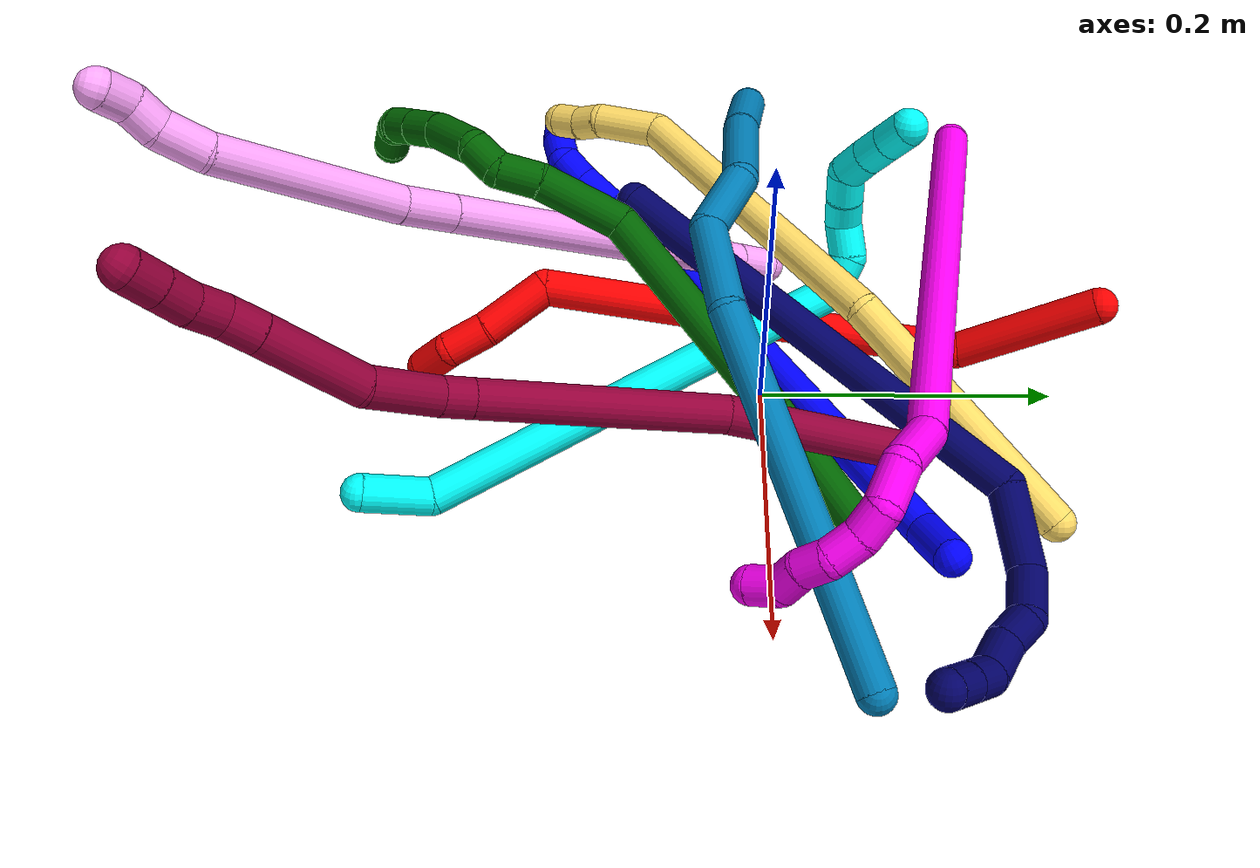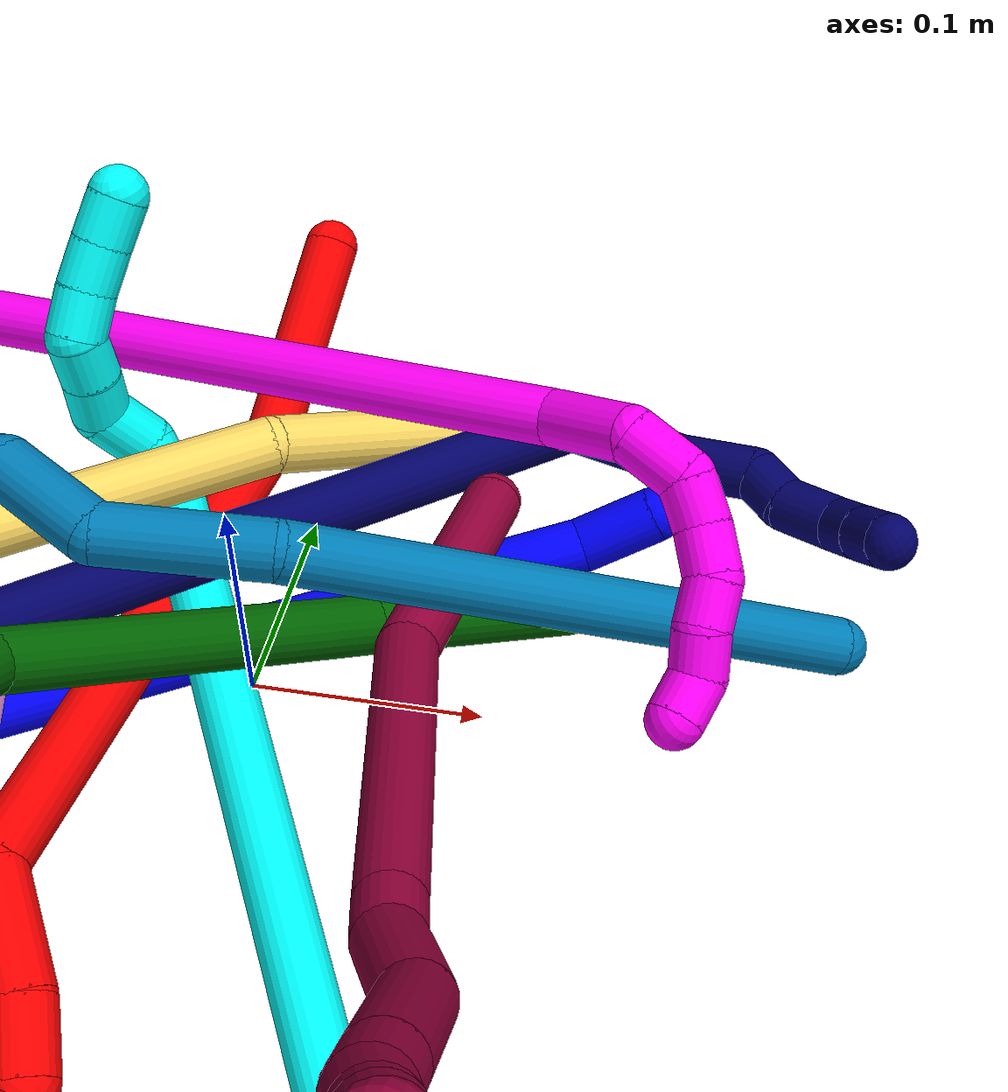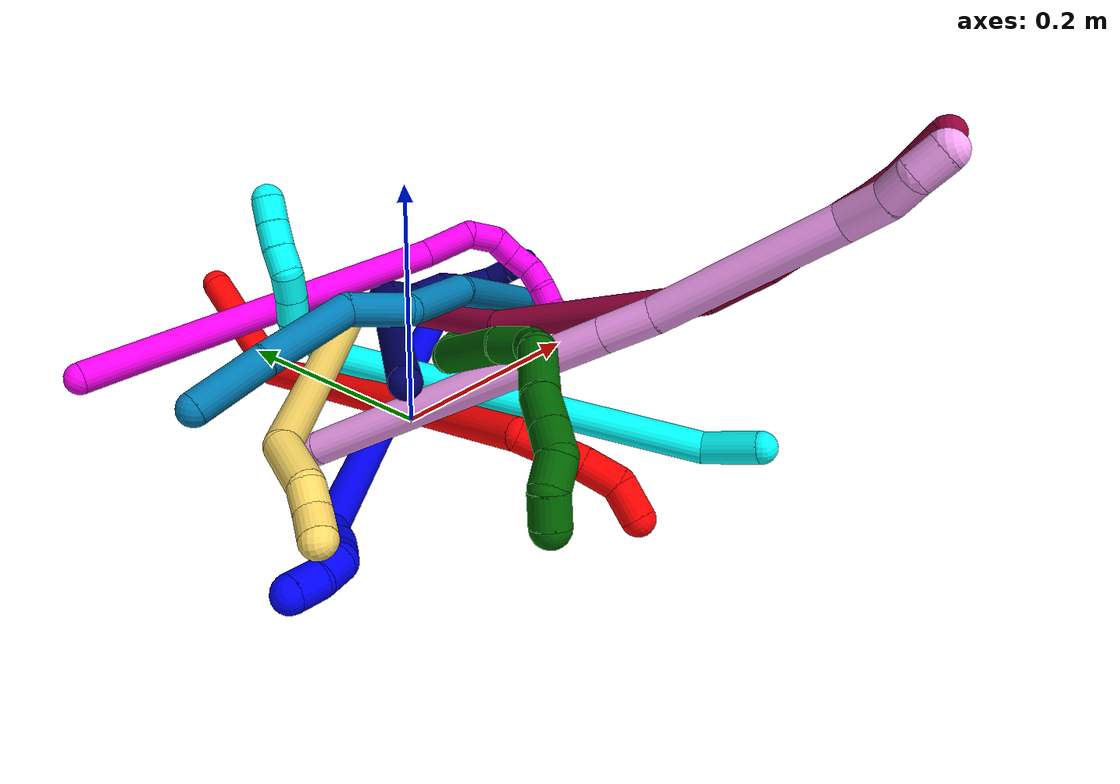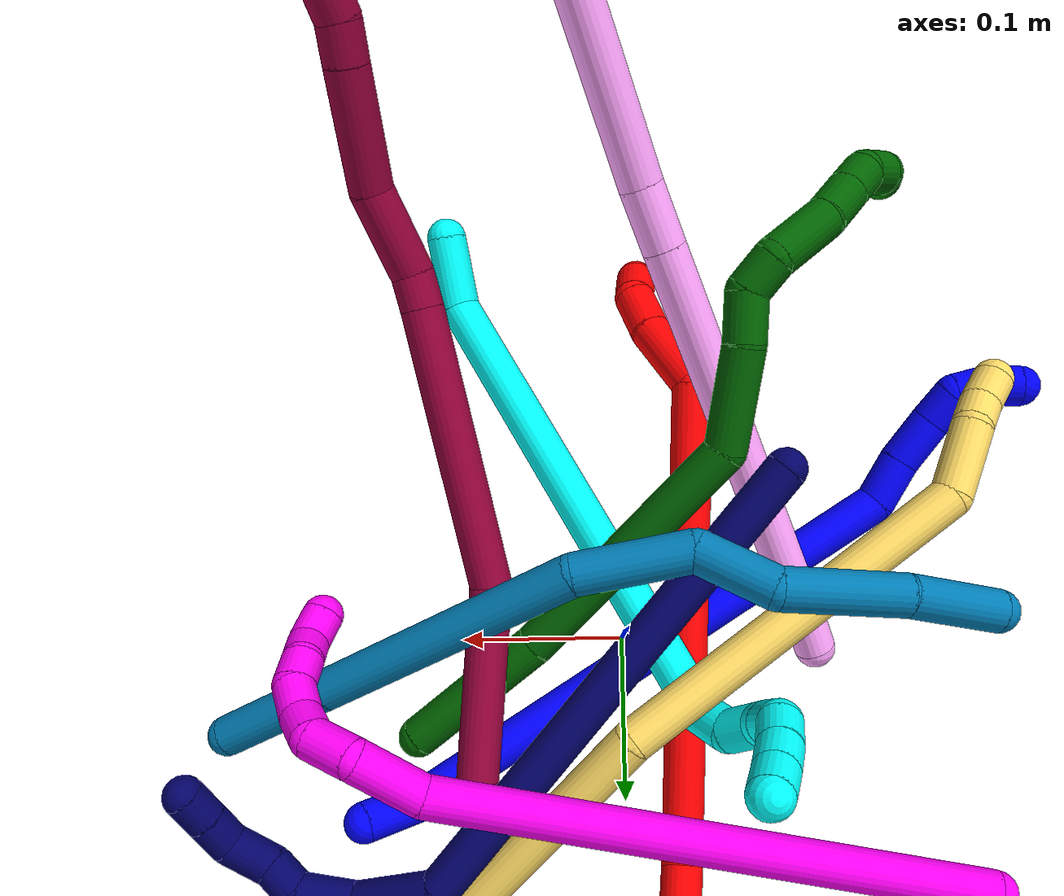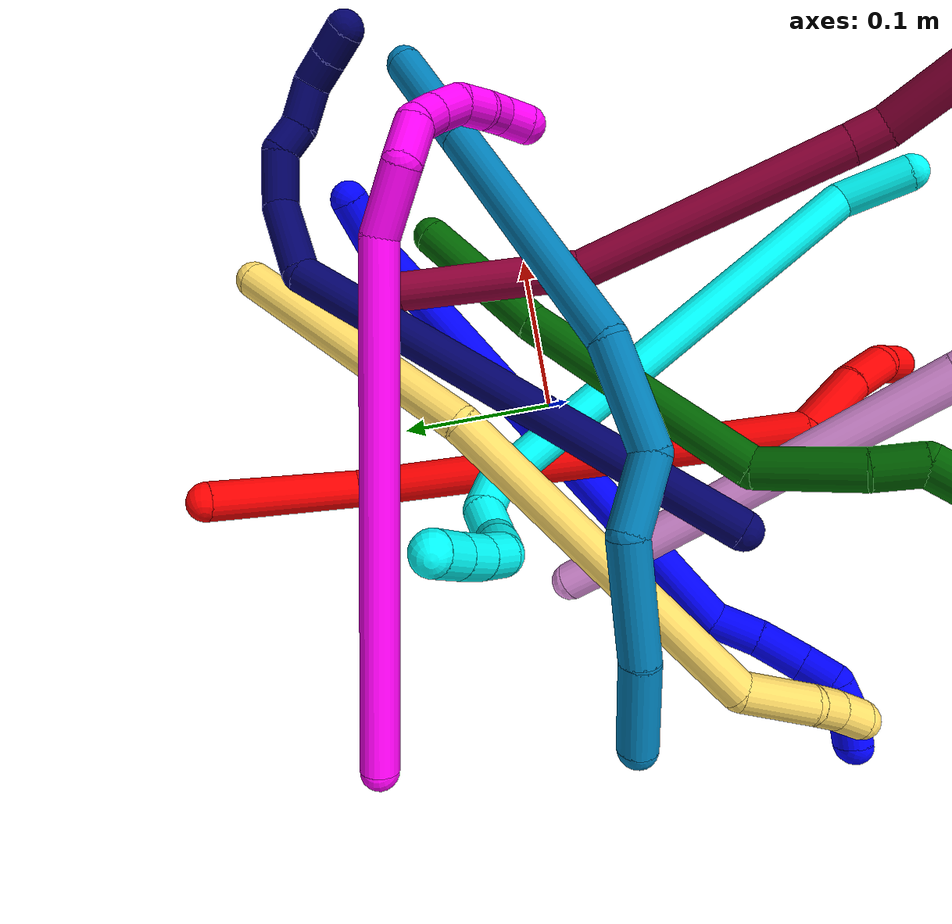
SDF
<sdf version="1.7">
 <world name="default">
  <plugin name="TubeGeneratorPlugin" filename="libtube_generator_plugin.so"/>
  <model name="photoneo_s_sensor">
   <static>1</static>
   <pose>0 0 2 1.57079 1.57079 3.14159</pose>
   <link name="link">
    <inertial><mass>0.1</mass></inertial>
    <sensor name="sensor" type="depth">
     <update_rate>30</update_rate>
     <camera>
      <horizontal_fov>1.22</horizontal_fov>
      <image><width>1920</width><height>1200</height><format>B8G8R8</format></image>
      <clip><near>0.1</near><far>4</far></clip>
      <depth_camera><output>points</output></depth_camera>
     </camera>
     <plugin name="camera_plugin" filename="libgazebo_ros_depth_camera.so">
      <baseline>0.2</baseline>
      <alwaysOn>1</alwaysOn>
      <updateRate>0.0</updateRate>
      <cameraName>camera_ir</cameraName>
      <imageTopicName>/camera/color/image_raw</imageTopicName>
      <cameraInfoTopicName>/camera/color/camera_info</cameraInfoTopicName>
      <depthImageTopicName>/camera/depth/image_raw</depthImageTopicName>
      <depthImageCameraInfoTopicName>/camera/depth/camera_info</depthImageCameraInfoTopicName>
      <pointCloudTopicName>/camera/depth/points</pointCloudTopicName>
      <frameName>fr_optical</frameName>
      <pointCloudCutoff>0.1</pointCloudCutoff>
      <pointCloudCutoffMax>2.0</pointCloudCutoffMax>
      <distortionK1>0</distortionK1>
      <distortionK2>0</distortionK2>
      <distortionK3>0</distortionK3>
      <distortionT1>0</distortionT1>
      <distortionT2>0</distortionT2>
      <CxPrime>0</CxPrime>
      <Cx>0</Cx>
      <Cy>0</Cy>
      <focalLength>0</focalLength>
      <hackBaseline>0</hackBaseline>
     </plugin>
    </sensor>
   </link>
  </model>
  <gravity>0 0 -9.8</gravity>
  <magnetic_field>6e-06 2.3e-05 -4.2e-05</magnetic_field>
  <atmosphere type="adiabatic"/>
  <physics name="default_physics" default="0" type="ode">
   <max_step_size>0.003</max_step_size>
   <real_time_factor>1</real_time_factor>
   <real_time_update_rate>1000</real_time_update_rate>
   <max_contacts>10000</max_contacts>
   <ode>
    <solver>
     <type>quick</type>
     <iters>100</iters>
     <sor>1.3</sor>
     <use_dynamic_moi_rescaling>0</use_dynamic_moi_rescaling>
    </solver>
    <constraints>
     <contact_max_correcting_vel>0</contact_max_correcting_vel>
     <contact_surface_layer>0.001</contact_surface_layer>
     <cfm>0</cfm>
     <erp>0.2</erp>
    </constraints>
   </ode>
  </physics>
  <scene><ambient>0.4 0.4 0.4 1</ambient><background>0.7 0.7 0.7 1</background><shadows>0</shadows></scene>
  <audio><device>default</device></audio>
  <spherical_coordinates>
   <surface_model>EARTH_WGS84</surface_model>
   <latitude_deg>0</latitude_deg>
   <longitude_deg>0</longitude_deg>
   <elevation>0</elevation>
   <heading_deg>0</heading_deg>
  </spherical_coordinates>
  <model name="bin">
   <static>1</static>
   <link name="bottom">
    <collision name="collision-bottom">
     <pose>0 0 -0.01 0 -0 0</pose>
     <geometry><box><size>0.8 0.6 0.02</size></box></geometry>
     <surface>
      <friction><ode><mu>100</mu><mu2>100</mu2></ode></friction>
      <contact><collide_bitmask>65535</collide_bitmask></contact>
     </surface>
    </collision>
   </link>
   <link name="west_wall">
    <collision name="collision-west_wall">
     <pose>-0.41 0 0.1 0 -0 0</pose>
     <geometry><box><size>0.02 0.6 0.2</size></box></geometry>
     <surface>
      <friction><ode><mu>100</mu><mu2>100</mu2></ode></friction>
      <contact><collide_bitmask>65535</collide_bitmask></contact>
     </surface>
    </collision>
   </link>
   <link name="east_wall">
    <collision name="collision-east_wall">
     <pose>0.41 0 0.1 0 -0 0</pose>
     <geometry><box><size>0.02 0.6 0.2</size></box></geometry>
     <surface>
      <friction><ode><mu>100</mu><mu2>100</mu2></ode></friction>
      <contact><collide_bitmask>65535</collide_bitmask></contact>
     </surface>
    </collision>
   </link>
   <link name="south_wall">
    <collision name="collision-south_wall">
     <pose>0 -0.31 0.1 0 -0 0</pose>
     <geometry><box><size>0.8 0.02 0.2</size></box></geometry>
     <surface>
      <friction><ode><mu>100</mu><mu2>100</mu2></ode></friction>
      <contact><collide_bitmask>65535</collide_bitmask></contact>
     </surface>
    </collision>
   </link>
   <link name="north_wall">
    <collision name="collision-north_wall">
     <pose>0 0.31 0.1 0 -0 0</pose>
     <geometry><box><size>0.8 0.02 0.2</size></box></geometry>
     <surface>
      <friction><ode><mu>100</mu><mu2>100</mu2></ode></friction>
      <contact><collide_bitmask>65535</collide_bitmask></contact>
     </surface>
    </collision>
   </link>
  </model>
  <model name="1">
   <static>0</static>
   <link name="1">
    <collision name="collision-cylinder-e_1_1_4">
     <pose>-0.016079 -0.007122 0.005715 0.894562 -1.05431 -0.544606</pose>
     <geometry><cylinder><radius>0.0125</radius><length>0.036982</length></cylinder></geometry>
     <surface>
      <friction><ode><mu>1.16</mu><mu2>1.16</mu2><slip1>0</slip1><slip2>0</slip2></ode></friction>
      <contact><ode><kp>1e+06</kp><kd>1</kd><max_vel>0</max_vel><min_depth>0.001</min_depth></ode></contact>
     </surface>
    </collision>
    <visual name="visual-cylinder-e_1_1_4">
     <pose>-0.016079 -0.007122 0.005715 0.894562 -1.05431 -0.544606</pose>
     <geometry><cylinder><radius>0.0125</radius><length>0.036982</length></cylinder></geometry>
     <material><ambient>0 0 1 1</ambient></material>
    </visual>
    <collision name="collision-cylinder-e_2_4_5">
     <pose>-0.137773 -0.077545 0.127361 0.499788 -0.674486 -0.17851</pose>
     <geometry><cylinder><radius>0.0125</radius><length>0.338241</length></cylinder></geometry>
     <surface>
      <friction><ode><mu>1.16</mu><mu2>1.16</mu2><slip1>0</slip1><slip2>0</slip2></ode></friction>
      <contact><ode><kp>1e+06</kp><kd>1</kd><max_vel>0</max_vel><min_depth>0.001</min_depth></ode></contact>
     </surface>
    </collision>
    <visual name="visual-cylinder-e_2_4_5">
     <pose>-0.137773 -0.077545 0.127361 0.499788 -0.674486 -0.17851</pose>
     <geometry><cylinder><radius>0.0125</radius><length>0.338241</length></cylinder></geometry>
     <material><ambient>0 0 1 1</ambient></material>
    </visual>
    <collision name="collision-cylinder-e_3_5_6">
     <pose>-0.245435 -0.1488 0.256181 0.552863 -0.134301 -0.038153</pose>
     <geometry><cylinder><radius>0.0125</radius><length>0.030565</length></cylinder></geometry>
     <surface>
      <friction><ode><mu>1.16</mu><mu2>1.16</mu2><slip1>0</slip1><slip2>0</slip2></ode></friction>
      <contact><ode><kp>1e+06</kp><kd>1</kd><max_vel>0</max_vel><min_depth>0.001</min_depth></ode></contact>
     </surface>
    </collision>
    <visual name="visual-cylinder-e_3_5_6">
     <pose>-0.245435 -0.1488 0.256181 0.552863 -0.134301 -0.038153</pose>
     <geometry><cylinder><radius>0.0125</radius><length>0.030565</length></cylinder></geometry>
     <material><ambient>0 0 1 1</ambient></material>
    </visual>
    <collision name="collision-cylinder-e_4_6_7">
     <pose>-0.250662 -0.16298 0.283043 0.419224 -0.20505 -0.043768</pose>
     <geometry><cylinder><radius>0.0125</radius><length>0.03125</length></cylinder></geometry>
     <surface>
      <friction><ode><mu>1.16</mu><mu2>1.16</mu2><slip1>0</slip1><slip2>0</slip2></ode></friction>
      <contact><ode><kp>1e+06</kp><kd>1</kd><max_vel>0</max_vel><min_depth>0.001</min_depth></ode></contact>
     </surface>
    </collision>
    <visual name="visual-cylinder-e_4_6_7">
     <pose>-0.250662 -0.16298 0.283043 0.419224 -0.20505 -0.043768</pose>
     <geometry><cylinder><radius>0.0125</radius><length>0.03125</length></cylinder></geometry>
     <material><ambient>0 0 1 1</ambient></material>
    </visual>
    <collision name="collision-cylinder-e_5_7_8">
     <pose>-0.25556 -0.172384 0.307364 0.297867 -0.157258 -0.023643</pose>
     <geometry><cylinder><radius>0.0125</radius><length>0.02192</length></cylinder></geometry>
     <surface>
      <friction><ode><mu>1.16</mu><mu2>1.16</mu2><slip1>0</slip1><slip2>0</slip2></ode></friction>
      <contact><ode><kp>1e+06</kp><kd>1</kd><max_vel>0</max_vel><min_depth>0.001</min_depth></ode></contact>
     </surface>
    </collision>
    <visual name="visual-cylinder-e_5_7_8">
     <pose>-0.25556 -0.172384 0.307364 0.297867 -0.157258 -0.023643</pose>
     <geometry><cylinder><radius>0.0125</radius><length>0.02192</length></cylinder></geometry>
     <material><ambient>0 0 1 1</ambient></material>
    </visual>
    <collision name="collision-cylinder-e_6_8_9">
     <pose>-0.265128 -0.176367 0.324406 0.119825 -0.861264 -0.055098</pose>
     <geometry><cylinder><radius>0.0125</radius><length>0.020698</length></cylinder></geometry>
     <surface>
      <friction><ode><mu>1.16</mu><mu2>1.16</mu2><slip1>0</slip1><slip2>0</slip2></ode></friction>
      <contact><ode><kp>1e+06</kp><kd>1</kd><max_vel>0</max_vel><min_depth>0.001</min_depth></ode></contact>
     </surface>
    </collision>
    <visual name="visual-cylinder-e_6_8_9">
     <pose>-0.265128 -0.176367 0.324406 0.119825 -0.861264 -0.055098</pose>
     <geometry><cylinder><radius>0.0125</radius><length>0.020698</length></cylinder></geometry>
     <material><ambient>0 0 1 1</ambient></material>
    </visual>
    <collision name="collision-cylinder-e_7_9_2">
     <pose>-0.281598 -0.175687 0.336295 -0.278605 -1.0108 0.154857</pose>
     <geometry><cylinder><radius>0.0125</radius><length>0.020344</length></cylinder></geometry>
     <surface>
      <friction><ode><mu>1.16</mu><mu2>1.16</mu2><slip1>0</slip1><slip2>0</slip2></ode></friction>
      <contact><ode><kp>1e+06</kp><kd>1</kd><max_vel>0</max_vel><min_depth>0.001</min_depth></ode></contact>
     </surface>
    </collision>
    <visual name="visual-cylinder-e_7_9_2">
     <pose>-0.281598 -0.175687 0.336295 -0.278605 -1.0108 0.154857</pose>
     <geometry><cylinder><radius>0.0125</radius><length>0.020344</length></cylinder></geometry>
     <material><ambient>0 0 1 1</ambient></material>
    </visual>
    <collision name="collision-sphere-2">
     <pose>-0.290216 -0.174201 0.341489 0 -0 0</pose>
     <geometry><sphere><radius>0.0125</radius></sphere></geometry>
     <surface>
      <friction><ode><mu>1.16</mu><mu2>1.16</mu2><slip1>0</slip1><slip2>0</slip2></ode></friction>
      <contact><ode><kp>1e+06</kp><kd>1</kd><max_vel>0</max_vel><min_depth>0.001</min_depth></ode></contact>
     </surface>
    </collision>
    <visual name="visual-sphere-2">
     <pose>-0.290216 -0.174201 0.341489 0 -0 0</pose>
     <geometry><sphere><radius>0.0125</radius></sphere></geometry>
     <material><ambient>0 0 1 1</ambient></material>
    </visual>
    <collision name="collision-sphere-9">
     <pose>-0.27298 -0.177173 0.3311 0 -0 0</pose>
     <geometry><sphere><radius>0.0125</radius></sphere></geometry>
     <surface>
      <friction><ode><mu>1.16</mu><mu2>1.16</mu2><slip1>0</slip1><slip2>0</slip2></ode></friction>
      <contact><ode><kp>1e+06</kp><kd>1</kd><max_vel>0</max_vel><min_depth>0.001</min_depth></ode></contact>
     </surface>
    </collision>
    <visual name="visual-sphere-9">
     <pose>-0.27298 -0.177173 0.3311 0 -0 0</pose>
     <geometry><sphere><radius>0.0125</radius></sphere></geometry>
     <material><ambient>0 0 1 1</ambient></material>
    </visual>
    <collision name="collision-sphere-4">
     <pose>-0.032158 -0.014244 0.01143 0 -0 0</pose>
     <geometry><sphere><radius>0.0125</radius></sphere></geometry>
     <surface>
      <friction><ode><mu>1.16</mu><mu2>1.16</mu2><slip1>0</slip1><slip2>0</slip2></ode></friction>
      <contact><ode><kp>1e+06</kp><kd>1</kd><max_vel>0</max_vel><min_depth>0.001</min_depth></ode></contact>
     </surface>
    </collision>
    <visual name="visual-sphere-4">
     <pose>-0.032158 -0.014244 0.01143 0 -0 0</pose>
     <geometry><sphere><radius>0.0125</radius></sphere></geometry>
     <material><ambient>0 0 1 1</ambient></material>
    </visual>
    <collision name="collision-sphere-1">
     <geometry><sphere><radius>0.0125</radius></sphere></geometry>
     <surface>
      <friction><ode><mu>1.16</mu><mu2>1.16</mu2><slip1>0</slip1><slip2>0</slip2></ode></friction>
      <contact><ode><kp>1e+06</kp><kd>1</kd><max_vel>0</max_vel><min_depth>0.001</min_depth></ode></contact>
     </surface>
    </collision>
    <visual name="visual-sphere-1">
     <geometry><sphere><radius>0.0125</radius></sphere></geometry>
     <material><ambient>0 0 1 1</ambient></material>
    </visual>
    <collision name="collision-sphere-8">
     <pose>-0.257277 -0.175561 0.317712 0 -0 0</pose>
     <geometry><sphere><radius>0.0125</radius></sphere></geometry>
     <surface>
      <friction><ode><mu>1.16</mu><mu2>1.16</mu2><slip1>0</slip1><slip2>0</slip2></ode></friction>
      <contact><ode><kp>1e+06</kp><kd>1</kd><max_vel>0</max_vel><min_depth>0.001</min_depth></ode></contact>
     </surface>
    </collision>
    <visual name="visual-sphere-8">
     <pose>-0.257277 -0.175561 0.317712 0 -0 0</pose>
     <geometry><sphere><radius>0.0125</radius></sphere></geometry>
     <material><ambient>0 0 1 1</ambient></material>
    </visual>
    <collision name="collision-sphere-5">
     <pose>-0.243388 -0.140847 0.243293 0 -0 0</pose>
     <geometry><sphere><radius>0.0125</radius></sphere></geometry>
     <surface>
      <friction><ode><mu>1.16</mu><mu2>1.16</mu2><slip1>0</slip1><slip2>0</slip2></ode></friction>
      <contact><ode><kp>1e+06</kp><kd>1</kd><max_vel>0</max_vel><min_depth>0.001</min_depth></ode></contact>
     </surface>
    </collision>
    <visual name="visual-sphere-5">
     <pose>-0.243388 -0.140847 0.243293 0 -0 0</pose>
     <geometry><sphere><radius>0.0125</radius></sphere></geometry>
     <material><ambient>0 0 1 1</ambient></material>
    </visual>
    <collision name="collision-sphere-6">
     <pose>-0.247481 -0.156753 0.26907 0 -0 0</pose>
     <geometry><sphere><radius>0.0125</radius></sphere></geometry>
     <surface>
      <friction><ode><mu>1.16</mu><mu2>1.16</mu2><slip1>0</slip1><slip2>0</slip2></ode></friction>
      <contact><ode><kp>1e+06</kp><kd>1</kd><max_vel>0</max_vel><min_depth>0.001</min_depth></ode></contact>
     </surface>
    </collision>
    <visual name="visual-sphere-6">
     <pose>-0.247481 -0.156753 0.26907 0 -0 0</pose>
     <geometry><sphere><radius>0.0125</radius></sphere></geometry>
     <material><ambient>0 0 1 1</ambient></material>
    </visual>
    <collision name="collision-sphere-7">
     <pose>-0.253844 -0.169207 0.297016 0 -0 0</pose>
     <geometry><sphere><radius>0.0125</radius></sphere></geometry>
     <surface>
      <friction><ode><mu>1.16</mu><mu2>1.16</mu2><slip1>0</slip1><slip2>0</slip2></ode></friction>
      <contact><ode><kp>1e+06</kp><kd>1</kd><max_vel>0</max_vel><min_depth>0.001</min_depth></ode></contact>
     </surface>
    </collision>
    <visual name="visual-sphere-7">
     <pose>-0.253844 -0.169207 0.297016 0 -0 0</pose>
     <geometry><sphere><radius>0.0125</radius></sphere></geometry>
     <material><ambient>0 0 1 1</ambient></material>
    </visual>
    <inertial>
     <pose>-0.158697 -0.094274 0.160518 0 -0 0</pose>
     <mass>0.5</mass>
     <inertia>
      <ixx>0.002028</ixx>
      <ixy>0</ixy>
      <ixz>0</ixz>
      <iyy>0.002521</iyy>
      <iyz>0</iyz>
      <izz>0.003276</izz>
     </inertia>
    </inertial>
   </link>
   <pose>0.156792 0.108735 0.02594 0.625298 -0.494492 -0.223409</pose>
  </model>
  <model name="2">
   <static>0</static>
   <link name="2">
    <collision name="collision-cylinder-e_1_1_4">
     <pose>0.00624 -0.048665 0.015079 1.27032 0.12188 0.089882</pose>
     <geometry><cylinder><radius>0.0125</radius><length>0.102658</length></cylinder></geometry>
     <surface>
      <friction><ode><mu>1.16</mu><mu2>1.16</mu2><slip1>0</slip1><slip2>0</slip2></ode></friction>
      <contact><ode><kp>1e+06</kp><kd>1</kd><max_vel>0</max_vel><min_depth>0.001</min_depth></ode></contact>
     </surface>
    </collision>
    <visual name="visual-cylinder-e_1_1_4">
     <pose>0.00624 -0.048665 0.015079 1.27032 0.12188 0.089882</pose>
     <geometry><cylinder><radius>0.0125</radius><length>0.102658</length></cylinder></geometry>
     <material><ambient>1 0 0 1</ambient></material>
    </visual>
    <collision name="collision-cylinder-e_2_4_5">
     <pose>-0.053662 -0.225991 0.010615 1.72155 -0.470234 -0.543576</pose>
     <geometry><cylinder><radius>0.0125</radius><length>0.291962</length></cylinder></geometry>
     <surface>
      <friction><ode><mu>1.16</mu><mu2>1.16</mu2><slip1>0</slip1><slip2>0</slip2></ode></friction>
      <contact><ode><kp>1e+06</kp><kd>1</kd><max_vel>0</max_vel><min_depth>0.001</min_depth></ode></contact>
     </surface>
    </collision>
    <visual name="visual-cylinder-e_2_4_5">
     <pose>-0.053662 -0.225991 0.010615 1.72155 -0.470234 -0.543576</pose>
     <geometry><cylinder><radius>0.0125</radius><length>0.291962</length></cylinder></geometry>
     <material><ambient>1 0 0 1</ambient></material>
    </visual>
    <collision name="collision-cylinder-e_3_5_6">
     <pose>-0.128522 -0.372348 0.005869 0.874342 -0.361264 -0.170277</pose>
     <geometry><cylinder><radius>0.0125</radius><length>0.04932</length></cylinder></geometry>
     <surface>
      <friction><ode><mu>1.16</mu><mu2>1.16</mu2><slip1>0</slip1><slip2>0</slip2></ode></friction>
      <contact><ode><kp>1e+06</kp><kd>1</kd><max_vel>0</max_vel><min_depth>0.001</min_depth></ode></contact>
     </surface>
    </collision>
    <visual name="visual-cylinder-e_3_5_6">
     <pose>-0.128522 -0.372348 0.005869 0.874342 -0.361264 -0.170277</pose>
     <geometry><cylinder><radius>0.0125</radius><length>0.04932</length></cylinder></geometry>
     <material><ambient>1 0 0 1</ambient></material>
    </visual>
    <collision name="collision-cylinder-e_4_6_7">
     <pose>-0.141117 -0.402124 0.027643 1.04713 -0.271236 -0.157228</pose>
     <geometry><cylinder><radius>0.0125</radius><length>0.028958</length></cylinder></geometry>
     <surface>
      <friction><ode><mu>1.16</mu><mu2>1.16</mu2><slip1>0</slip1><slip2>0</slip2></ode></friction>
      <contact><ode><kp>1e+06</kp><kd>1</kd><max_vel>0</max_vel><min_depth>0.001</min_depth></ode></contact>
     </surface>
    </collision>
    <visual name="visual-cylinder-e_4_6_7">
     <pose>-0.141117 -0.402124 0.027643 1.04713 -0.271236 -0.157228</pose>
     <geometry><cylinder><radius>0.0125</radius><length>0.028958</length></cylinder></geometry>
     <material><ambient>1 0 0 1</ambient></material>
    </visual>
    <collision name="collision-cylinder-e_5_7_2">
     <pose>-0.141296 -0.425882 0.040413 1.11019 0.27656 0.17218</pose>
     <geometry><cylinder><radius>0.0125</radius><length>0.027103</length></cylinder></geometry>
     <surface>
      <friction><ode><mu>1.16</mu><mu2>1.16</mu2><slip1>0</slip1><slip2>0</slip2></ode></friction>
      <contact><ode><kp>1e+06</kp><kd>1</kd><max_vel>0</max_vel><min_depth>0.001</min_depth></ode></contact>
     </surface>
    </collision>
    <visual name="visual-cylinder-e_5_7_2">
     <pose>-0.141296 -0.425882 0.040413 1.11019 0.27656 0.17218</pose>
     <geometry><cylinder><radius>0.0125</radius><length>0.027103</length></cylinder></geometry>
     <material><ambient>1 0 0 1</ambient></material>
    </visual>
    <collision name="collision-sphere-2">
     <pose>-0.137596 -0.43756 0.046208 0 -0 0</pose>
     <geometry><sphere><radius>0.0125</radius></sphere></geometry>
     <surface>
      <friction><ode><mu>1.16</mu><mu2>1.16</mu2><slip1>0</slip1><slip2>0</slip2></ode></friction>
      <contact><ode><kp>1e+06</kp><kd>1</kd><max_vel>0</max_vel><min_depth>0.001</min_depth></ode></contact>
     </surface>
    </collision>
    <visual name="visual-sphere-2">
     <pose>-0.137596 -0.43756 0.046208 0 -0 0</pose>
     <geometry><sphere><radius>0.0125</radius></sphere></geometry>
     <material><ambient>1 0 0 1</ambient></material>
    </visual>
    <collision name="collision-sphere-7">
     <pose>-0.144996 -0.414204 0.034619 0 -0 0</pose>
     <geometry><sphere><radius>0.0125</radius></sphere></geometry>
     <surface>
      <friction><ode><mu>1.16</mu><mu2>1.16</mu2><slip1>0</slip1><slip2>0</slip2></ode></friction>
      <contact><ode><kp>1e+06</kp><kd>1</kd><max_vel>0</max_vel><min_depth>0.001</min_depth></ode></contact>
     </surface>
    </collision>
    <visual name="visual-sphere-7">
     <pose>-0.144996 -0.414204 0.034619 0 -0 0</pose>
     <geometry><sphere><radius>0.0125</radius></sphere></geometry>
     <material><ambient>1 0 0 1</ambient></material>
    </visual>
    <collision name="collision-sphere-6">
     <pose>-0.137238 -0.390044 0.020667 0 -0 0</pose>
     <geometry><sphere><radius>0.0125</radius></sphere></geometry>
     <surface>
      <friction><ode><mu>1.16</mu><mu2>1.16</mu2><slip1>0</slip1><slip2>0</slip2></ode></friction>
      <contact><ode><kp>1e+06</kp><kd>1</kd><max_vel>0</max_vel><min_depth>0.001</min_depth></ode></contact>
     </surface>
    </collision>
    <visual name="visual-sphere-6">
     <pose>-0.137238 -0.390044 0.020667 0 -0 0</pose>
     <geometry><sphere><radius>0.0125</radius></sphere></geometry>
     <material><ambient>1 0 0 1</ambient></material>
    </visual>
    <collision name="collision-sphere-5">
     <pose>-0.119805 -0.354652 -0.008929 0 -0 0</pose>
     <geometry><sphere><radius>0.0125</radius></sphere></geometry>
     <surface>
      <friction><ode><mu>1.16</mu><mu2>1.16</mu2><slip1>0</slip1><slip2>0</slip2></ode></friction>
      <contact><ode><kp>1e+06</kp><kd>1</kd><max_vel>0</max_vel><min_depth>0.001</min_depth></ode></contact>
     </surface>
    </collision>
    <visual name="visual-sphere-5">
     <pose>-0.119805 -0.354652 -0.008929 0 -0 0</pose>
     <geometry><sphere><radius>0.0125</radius></sphere></geometry>
     <material><ambient>1 0 0 1</ambient></material>
    </visual>
    <collision name="collision-sphere-1">
     <geometry><sphere><radius>0.0125</radius></sphere></geometry>
     <surface>
      <friction><ode><mu>1.16</mu><mu2>1.16</mu2><slip1>0</slip1><slip2>0</slip2></ode></friction>
      <contact><ode><kp>1e+06</kp><kd>1</kd><max_vel>0</max_vel><min_depth>0.001</min_depth></ode></contact>
     </surface>
    </collision>
    <visual name="visual-sphere-1">
     <geometry><sphere><radius>0.0125</radius></sphere></geometry>
     <material><ambient>1 0 0 1</ambient></material>
    </visual>
    <collision name="collision-sphere-4">
     <pose>0.012481 -0.097331 0.030159 0 -0 0</pose>
     <geometry><sphere><radius>0.0125</radius></sphere></geometry>
     <surface>
      <friction><ode><mu>1.16</mu><mu2>1.16</mu2><slip1>0</slip1><slip2>0</slip2></ode></friction>
      <contact><ode><kp>1e+06</kp><kd>1</kd><max_vel>0</max_vel><min_depth>0.001</min_depth></ode></contact>
     </surface>
    </collision>
    <visual name="visual-sphere-4">
     <pose>0.012481 -0.097331 0.030159 0 -0 0</pose>
     <geometry><sphere><radius>0.0125</radius></sphere></geometry>
     <material><ambient>1 0 0 1</ambient></material>
    </visual>
    <inertial>
     <pose>-0.058563 -0.225056 0.013665 0 -0 0</pose>
     <mass>0.5</mass>
     <inertia>
      <ixx>0.000735</ixx>
      <ixy>0</ixy>
      <ixz>0</ixz>
      <iyy>-0.000734</iyy>
      <iyz>0</iyz>
      <izz>0.002882</izz>
     </inertia>
    </inertial>
   </link>
   <pose>-0.021127 0.224883 0.067149 2.77171 0.743252 2.61111</pose>
  </model>
  <model name="3">
   <static>0</static>
   <link name="3">
    <collision name="collision-cylinder-e_1_1_4">
     <pose>-0.006111 0.021664 -0.004927 -1.79442 -0.268433 0.335196</pose>
     <geometry><cylinder><radius>0.0125</radius><length>0.046085</length></cylinder></geometry>
     <surface>
      <friction><ode><mu>1.16</mu><mu2>1.16</mu2><slip1>0</slip1><slip2>0</slip2></ode></friction>
      <contact><ode><kp>1e+06</kp><kd>1</kd><max_vel>0</max_vel><min_depth>0.001</min_depth></ode></contact>
     </surface>
    </collision>
    <visual name="visual-cylinder-e_1_1_4">
     <pose>-0.006111 0.021664 -0.004927 -1.79442 -0.268433 0.335196</pose>
     <geometry><cylinder><radius>0.0125</radius><length>0.046085</length></cylinder></geometry>
     <material><ambient>0.003922 1 0.996078 1</ambient></material>
    </visual>
    <collision name="collision-cylinder-e_2_4_5">
     <pose>-0.085001 0.169545 0.03139 -1.25497 -0.501376 0.367261</pose>
     <geometry><cylinder><radius>0.0125</radius><length>0.302843</length></cylinder></geometry>
     <surface>
      <friction><ode><mu>1.16</mu><mu2>1.16</mu2><slip1>0</slip1><slip2>0</slip2></ode></friction>
      <contact><ode><kp>1e+06</kp><kd>1</kd><max_vel>0</max_vel><min_depth>0.001</min_depth></ode></contact>
     </surface>
    </collision>
    <visual name="visual-cylinder-e_2_4_5">
     <pose>-0.085001 0.169545 0.03139 -1.25497 -0.501376 0.367261</pose>
     <geometry><cylinder><radius>0.0125</radius><length>0.302843</length></cylinder></geometry>
     <material><ambient>0.003922 1 0.996078 1</ambient></material>
    </visual>
    <collision name="collision-cylinder-e_3_5_6">
     <pose>-0.163051 0.300483 0.083798 -0.400087 -0.41027 0.084321</pose>
     <geometry><cylinder><radius>0.0125</radius><length>0.026436</length></cylinder></geometry>
     <surface>
      <friction><ode><mu>1.16</mu><mu2>1.16</mu2><slip1>0</slip1><slip2>0</slip2></ode></friction>
      <contact><ode><kp>1e+06</kp><kd>1</kd><max_vel>0</max_vel><min_depth>0.001</min_depth></ode></contact>
     </surface>
    </collision>
    <visual name="visual-cylinder-e_3_5_6">
     <pose>-0.163051 0.300483 0.083798 -0.400087 -0.41027 0.084321</pose>
     <geometry><cylinder><radius>0.0125</radius><length>0.026436</length></cylinder></geometry>
     <material><ambient>0.003922 1 0.996078 1</ambient></material>
    </visual>
    <collision name="collision-cylinder-e_4_6_7">
     <pose>-0.174415 0.302516 0.105069 0.259985 -0.527387 -0.07056</pose>
     <geometry><cylinder><radius>0.0125</radius><length>0.024208</length></cylinder></geometry>
     <surface>
      <friction><ode><mu>1.16</mu><mu2>1.16</mu2><slip1>0</slip1><slip2>0</slip2></ode></friction>
      <contact><ode><kp>1e+06</kp><kd>1</kd><max_vel>0</max_vel><min_depth>0.001</min_depth></ode></contact>
     </surface>
    </collision>
    <visual name="visual-cylinder-e_4_6_7">
     <pose>-0.174415 0.302516 0.105069 0.259985 -0.527387 -0.07056</pose>
     <geometry><cylinder><radius>0.0125</radius><length>0.024208</length></cylinder></geometry>
     <material><ambient>0.003922 1 0.996078 1</ambient></material>
    </visual>
    <collision name="collision-cylinder-e_5_7_8">
     <pose>-0.179202 0.299089 0.125092 0.074293 0.130461 0.004855</pose>
     <geometry><cylinder><radius>0.0125</radius><length>0.020054</length></cylinder></geometry>
     <surface>
      <friction><ode><mu>1.16</mu><mu2>1.16</mu2><slip1>0</slip1><slip2>0</slip2></ode></friction>
      <contact><ode><kp>1e+06</kp><kd>1</kd><max_vel>0</max_vel><min_depth>0.001</min_depth></ode></contact>
     </surface>
    </collision>
    <visual name="visual-cylinder-e_5_7_8">
     <pose>-0.179202 0.299089 0.125092 0.074293 0.130461 0.004855</pose>
     <geometry><cylinder><radius>0.0125</radius><length>0.020054</length></cylinder></geometry>
     <material><ambient>0.003922 1 0.996078 1</ambient></material>
    </visual>
    <collision name="collision-cylinder-e_6_8_9">
     <pose>-0.177479 0.297739 0.145123 0.060454 0.041287 0.001249</pose>
     <geometry><cylinder><radius>0.0125</radius><length>0.020288</length></cylinder></geometry>
     <surface>
      <friction><ode><mu>1.16</mu><mu2>1.16</mu2><slip1>0</slip1><slip2>0</slip2></ode></friction>
      <contact><ode><kp>1e+06</kp><kd>1</kd><max_vel>0</max_vel><min_depth>0.001</min_depth></ode></contact>
     </surface>
    </collision>
    <visual name="visual-cylinder-e_6_8_9">
     <pose>-0.177479 0.297739 0.145123 0.060454 0.041287 0.001249</pose>
     <geometry><cylinder><radius>0.0125</radius><length>0.020288</length></cylinder></geometry>
     <material><ambient>0.003922 1 0.996078 1</ambient></material>
    </visual>
    <collision name="collision-cylinder-e_7_9_10">
     <pose>-0.174476 0.302792 0.163095 -0.624821 0.260783 -0.08466</pose>
     <geometry><cylinder><radius>0.0125</radius><length>0.02005</length></cylinder></geometry>
     <surface>
      <friction><ode><mu>1.16</mu><mu2>1.16</mu2><slip1>0</slip1><slip2>0</slip2></ode></friction>
      <contact><ode><kp>1e+06</kp><kd>1</kd><max_vel>0</max_vel><min_depth>0.001</min_depth></ode></contact>
     </surface>
    </collision>
    <visual name="visual-cylinder-e_7_9_10">
     <pose>-0.174476 0.302792 0.163095 -0.624821 0.260783 -0.08466</pose>
     <geometry><cylinder><radius>0.0125</radius><length>0.02005</length></cylinder></geometry>
     <material><ambient>0.003922 1 0.996078 1</ambient></material>
    </visual>
    <collision name="collision-cylinder-e_8_10_11">
     <pose>-0.16836 0.313963 0.178527 -0.628349 0.36058 -0.118314</pose>
     <geometry><cylinder><radius>0.0125</radius><length>0.020018</length></cylinder></geometry>
     <surface>
      <friction><ode><mu>1.16</mu><mu2>1.16</mu2><slip1>0</slip1><slip2>0</slip2></ode></friction>
      <contact><ode><kp>1e+06</kp><kd>1</kd><max_vel>0</max_vel><min_depth>0.001</min_depth></ode></contact>
     </surface>
    </collision>
    <visual name="visual-cylinder-e_8_10_11">
     <pose>-0.16836 0.313963 0.178527 -0.628349 0.36058 -0.118314</pose>
     <geometry><cylinder><radius>0.0125</radius><length>0.020018</length></cylinder></geometry>
     <material><ambient>0.003922 1 0.996078 1</ambient></material>
    </visual>
    <collision name="collision-cylinder-e_9_11_2">
     <pose>-0.160944 0.324743 0.193672 -0.60876 0.398472 -0.12669</pose>
     <geometry><cylinder><radius>0.0125</radius><length>0.020019</length></cylinder></geometry>
     <surface>
      <friction><ode><mu>1.16</mu><mu2>1.16</mu2><slip1>0</slip1><slip2>0</slip2></ode></friction>
      <contact><ode><kp>1e+06</kp><kd>1</kd><max_vel>0</max_vel><min_depth>0.001</min_depth></ode></contact>
     </surface>
    </collision>
    <visual name="visual-cylinder-e_9_11_2">
     <pose>-0.160944 0.324743 0.193672 -0.60876 0.398472 -0.12669</pose>
     <geometry><cylinder><radius>0.0125</radius><length>0.020019</length></cylinder></geometry>
     <material><ambient>0.003922 1 0.996078 1</ambient></material>
    </visual>
    <collision name="collision-sphere-2">
     <pose>-0.157061 0.330019 0.20124 0 -0 0</pose>
     <geometry><sphere><radius>0.0125</radius></sphere></geometry>
     <surface>
      <friction><ode><mu>1.16</mu><mu2>1.16</mu2><slip1>0</slip1><slip2>0</slip2></ode></friction>
      <contact><ode><kp>1e+06</kp><kd>1</kd><max_vel>0</max_vel><min_depth>0.001</min_depth></ode></contact>
     </surface>
    </collision>
    <visual name="visual-sphere-2">
     <pose>-0.157061 0.330019 0.20124 0 -0 0</pose>
     <geometry><sphere><radius>0.0125</radius></sphere></geometry>
     <material><ambient>0.003922 1 0.996078 1</ambient></material>
    </visual>
    <collision name="collision-sphere-11">
     <pose>-0.164828 0.319468 0.186104 0 -0 0</pose>
     <geometry><sphere><radius>0.0125</radius></sphere></geometry>
     <surface>
      <friction><ode><mu>1.16</mu><mu2>1.16</mu2><slip1>0</slip1><slip2>0</slip2></ode></friction>
      <contact><ode><kp>1e+06</kp><kd>1</kd><max_vel>0</max_vel><min_depth>0.001</min_depth></ode></contact>
     </surface>
    </collision>
    <visual name="visual-sphere-11">
     <pose>-0.164828 0.319468 0.186104 0 -0 0</pose>
     <geometry><sphere><radius>0.0125</radius></sphere></geometry>
     <material><ambient>0.003922 1 0.996078 1</ambient></material>
    </visual>
    <collision name="collision-sphere-10">
     <pose>-0.171891 0.308458 0.170951 0 -0 0</pose>
     <geometry><sphere><radius>0.0125</radius></sphere></geometry>
     <surface>
      <friction><ode><mu>1.16</mu><mu2>1.16</mu2><slip1>0</slip1><slip2>0</slip2></ode></friction>
      <contact><ode><kp>1e+06</kp><kd>1</kd><max_vel>0</max_vel><min_depth>0.001</min_depth></ode></contact>
     </surface>
    </collision>
    <visual name="visual-sphere-10">
     <pose>-0.171891 0.308458 0.170951 0 -0 0</pose>
     <geometry><sphere><radius>0.0125</radius></sphere></geometry>
     <material><ambient>0.003922 1 0.996078 1</ambient></material>
    </visual>
    <collision name="collision-sphere-9">
     <pose>-0.17706 0.297126 0.155239 0 -0 0</pose>
     <geometry><sphere><radius>0.0125</radius></sphere></geometry>
     <surface>
      <friction><ode><mu>1.16</mu><mu2>1.16</mu2><slip1>0</slip1><slip2>0</slip2></ode></friction>
      <contact><ode><kp>1e+06</kp><kd>1</kd><max_vel>0</max_vel><min_depth>0.001</min_depth></ode></contact>
     </surface>
    </collision>
    <visual name="visual-sphere-9">
     <pose>-0.17706 0.297126 0.155239 0 -0 0</pose>
     <geometry><sphere><radius>0.0125</radius></sphere></geometry>
     <material><ambient>0.003922 1 0.996078 1</ambient></material>
    </visual>
    <collision name="collision-sphere-4">
     <pose>-0.012223 0.043328 -0.009854 0 -0 0</pose>
     <geometry><sphere><radius>0.0125</radius></sphere></geometry>
     <surface>
      <friction><ode><mu>1.16</mu><mu2>1.16</mu2><slip1>0</slip1><slip2>0</slip2></ode></friction>
      <contact><ode><kp>1e+06</kp><kd>1</kd><max_vel>0</max_vel><min_depth>0.001</min_depth></ode></contact>
     </surface>
    </collision>
    <visual name="visual-sphere-4">
     <pose>-0.012223 0.043328 -0.009854 0 -0 0</pose>
     <geometry><sphere><radius>0.0125</radius></sphere></geometry>
     <material><ambient>0.003922 1 0.996078 1</ambient></material>
    </visual>
    <collision name="collision-sphere-1">
     <geometry><sphere><radius>0.0125</radius></sphere></geometry>
     <surface>
      <friction><ode><mu>1.16</mu><mu2>1.16</mu2><slip1>0</slip1><slip2>0</slip2></ode></friction>
      <contact><ode><kp>1e+06</kp><kd>1</kd><max_vel>0</max_vel><min_depth>0.001</min_depth></ode></contact>
     </surface>
    </collision>
    <visual name="visual-sphere-1">
     <geometry><sphere><radius>0.0125</radius></sphere></geometry>
     <material><ambient>0.003922 1 0.996078 1</ambient></material>
    </visual>
    <collision name="collision-sphere-8">
     <pose>-0.177898 0.298351 0.135006 0 -0 0</pose>
     <geometry><sphere><radius>0.0125</radius></sphere></geometry>
     <surface>
      <friction><ode><mu>1.16</mu><mu2>1.16</mu2><slip1>0</slip1><slip2>0</slip2></ode></friction>
      <contact><ode><kp>1e+06</kp><kd>1</kd><max_vel>0</max_vel><min_depth>0.001</min_depth></ode></contact>
     </surface>
    </collision>
    <visual name="visual-sphere-8">
     <pose>-0.177898 0.298351 0.135006 0 -0 0</pose>
     <geometry><sphere><radius>0.0125</radius></sphere></geometry>
     <material><ambient>0.003922 1 0.996078 1</ambient></material>
    </visual>
    <collision name="collision-sphere-5">
     <pose>-0.157779 0.295762 0.072634 0 -0 0</pose>
     <geometry><sphere><radius>0.0125</radius></sphere></geometry>
     <surface>
      <friction><ode><mu>1.16</mu><mu2>1.16</mu2><slip1>0</slip1><slip2>0</slip2></ode></friction>
      <contact><ode><kp>1e+06</kp><kd>1</kd><max_vel>0</max_vel><min_depth>0.001</min_depth></ode></contact>
     </surface>
    </collision>
    <visual name="visual-sphere-5">
     <pose>-0.157779 0.295762 0.072634 0 -0 0</pose>
     <geometry><sphere><radius>0.0125</radius></sphere></geometry>
     <material><ambient>0.003922 1 0.996078 1</ambient></material>
    </visual>
    <collision name="collision-sphere-6">
     <pose>-0.168323 0.305204 0.094961 0 -0 0</pose>
     <geometry><sphere><radius>0.0125</radius></sphere></geometry>
     <surface>
      <friction><ode><mu>1.16</mu><mu2>1.16</mu2><slip1>0</slip1><slip2>0</slip2></ode></friction>
      <contact><ode><kp>1e+06</kp><kd>1</kd><max_vel>0</max_vel><min_depth>0.001</min_depth></ode></contact>
     </surface>
    </collision>
    <visual name="visual-sphere-6">
     <pose>-0.168323 0.305204 0.094961 0 -0 0</pose>
     <geometry><sphere><radius>0.0125</radius></sphere></geometry>
     <material><ambient>0.003922 1 0.996078 1</ambient></material>
    </visual>
    <collision name="collision-sphere-7">
     <pose>-0.180507 0.299827 0.115178 0 -0 0</pose>
     <geometry><sphere><radius>0.0125</radius></sphere></geometry>
     <surface>
      <friction><ode><mu>1.16</mu><mu2>1.16</mu2><slip1>0</slip1><slip2>0</slip2></ode></friction>
      <contact><ode><kp>1e+06</kp><kd>1</kd><max_vel>0</max_vel><min_depth>0.001</min_depth></ode></contact>
     </surface>
    </collision>
    <visual name="visual-sphere-7">
     <pose>-0.180507 0.299827 0.115178 0 -0 0</pose>
     <geometry><sphere><radius>0.0125</radius></sphere></geometry>
     <material><ambient>0.003922 1 0.996078 1</ambient></material>
    </visual>
    <inertial>
     <pose>-0.103682 0.197012 0.060423 0 -0 0</pose>
     <mass>0.5</mass>
     <inertia>
      <ixx>0.002647</ixx>
      <ixy>0</ixy>
      <ixz>0</ixz>
      <iyy>0.001827</iyy>
      <iyz>0</iyz>
      <izz>-0.000814</izz>
     </inertia>
    </inertial>
   </link>
   <pose>0.108846 -0.258833 0.024813 -0.035286 -0.173302 -0.050997</pose>
  </model>
  <model name="4">
   <static>0</static>
   <link name="4">
    <collision name="collision-cylinder-e_1_1_4">
     <pose>0.000991 -0.002826 0.013912 0.200398 0.069666 0.007007</pose>
     <geometry><cylinder><radius>0.0125</radius><length>0.028461</length></cylinder></geometry>
     <surface>
      <friction><ode><mu>1.16</mu><mu2>1.16</mu2><slip1>0</slip1><slip2>0</slip2></ode></friction>
      <contact><ode><kp>1e+06</kp><kd>1</kd><max_vel>0</max_vel><min_depth>0.001</min_depth></ode></contact>
     </surface>
    </collision>
    <visual name="visual-cylinder-e_1_1_4">
     <pose>0.000991 -0.002826 0.013912 0.200398 0.069666 0.007007</pose>
     <geometry><cylinder><radius>0.0125</radius><length>0.028461</length></cylinder></geometry>
     <material><ambient>1 0.65098 0.996078 1</ambient></material>
    </visual>
    <collision name="collision-cylinder-e_2_4_5">
     <pose>0.011277 -0.032219 0.14381 0.225172 0.077968 0.00882</pose>
     <geometry><cylinder><radius>0.0125</radius><length>0.238705</length></cylinder></geometry>
     <surface>
      <friction><ode><mu>1.16</mu><mu2>1.16</mu2><slip1>0</slip1><slip2>0</slip2></ode></friction>
      <contact><ode><kp>1e+06</kp><kd>1</kd><max_vel>0</max_vel><min_depth>0.001</min_depth></ode></contact>
     </surface>
    </collision>
    <visual name="visual-cylinder-e_2_4_5">
     <pose>0.011277 -0.032219 0.14381 0.225172 0.077968 0.00882</pose>
     <geometry><cylinder><radius>0.0125</radius><length>0.238705</length></cylinder></geometry>
     <material><ambient>1 0.65098 0.996078 1</ambient></material>
    </visual>
    <collision name="collision-cylinder-e_3_5_6">
     <pose>0.021858 -0.062683 0.277389 0.217967 0.071148 0.007788</pose>
     <geometry><cylinder><radius>0.0125</radius><length>0.036132</length></cylinder></geometry>
     <surface>
      <friction><ode><mu>1.16</mu><mu2>1.16</mu2><slip1>0</slip1><slip2>0</slip2></ode></friction>
      <contact><ode><kp>1e+06</kp><kd>1</kd><max_vel>0</max_vel><min_depth>0.001</min_depth></ode></contact>
     </surface>
    </collision>
    <visual name="visual-cylinder-e_3_5_6">
     <pose>0.021858 -0.062683 0.277389 0.217967 0.071148 0.007788</pose>
     <geometry><cylinder><radius>0.0125</radius><length>0.036132</length></cylinder></geometry>
     <material><ambient>1 0.65098 0.996078 1</ambient></material>
    </visual>
    <collision name="collision-cylinder-e_4_6_7">
     <pose>0.032882 -0.077482 0.356589 0.175145 0.154441 0.013586</pose>
     <geometry><cylinder><radius>0.0125</radius><length>0.126634</length></cylinder></geometry>
     <surface>
      <friction><ode><mu>1.16</mu><mu2>1.16</mu2><slip1>0</slip1><slip2>0</slip2></ode></friction>
      <contact><ode><kp>1e+06</kp><kd>1</kd><max_vel>0</max_vel><min_depth>0.001</min_depth></ode></contact>
     </surface>
    </collision>
    <visual name="visual-cylinder-e_4_6_7">
     <pose>0.032882 -0.077482 0.356589 0.175145 0.154441 0.013586</pose>
     <geometry><cylinder><radius>0.0125</radius><length>0.126634</length></cylinder></geometry>
     <material><ambient>1 0.65098 0.996078 1</ambient></material>
    </visual>
    <collision name="collision-cylinder-e_5_7_8">
     <pose>0.045166 -0.087261 0.432945 -0.075944 0.170285 -0.006485</pose>
     <geometry><cylinder><radius>0.0125</radius><length>0.030018</length></cylinder></geometry>
     <surface>
      <friction><ode><mu>1.16</mu><mu2>1.16</mu2><slip1>0</slip1><slip2>0</slip2></ode></friction>
      <contact><ode><kp>1e+06</kp><kd>1</kd><max_vel>0</max_vel><min_depth>0.001</min_depth></ode></contact>
     </surface>
    </collision>
    <visual name="visual-cylinder-e_5_7_8">
     <pose>0.045166 -0.087261 0.432945 -0.075944 0.170285 -0.006485</pose>
     <geometry><cylinder><radius>0.0125</radius><length>0.030018</length></cylinder></geometry>
     <material><ambient>1 0.65098 0.996078 1</ambient></material>
    </visual>
    <collision name="collision-cylinder-e_6_8_9">
     <pose>0.051505 -0.083493 0.456583 -0.289318 0.388526 -0.057306</pose>
     <geometry><cylinder><radius>0.0125</radius><length>0.020042</length></cylinder></geometry>
     <surface>
      <friction><ode><mu>1.16</mu><mu2>1.16</mu2><slip1>0</slip1><slip2>0</slip2></ode></friction>
      <contact><ode><kp>1e+06</kp><kd>1</kd><max_vel>0</max_vel><min_depth>0.001</min_depth></ode></contact>
     </surface>
    </collision>
    <visual name="visual-cylinder-e_6_8_9">
     <pose>0.051505 -0.083493 0.456583 -0.289318 0.388526 -0.057306</pose>
     <geometry><cylinder><radius>0.0125</radius><length>0.020042</length></cylinder></geometry>
     <material><ambient>1 0.65098 0.996078 1</ambient></material>
    </visual>
    <collision name="collision-cylinder-e_7_9_2">
     <pose>0.058998 -0.082677 0.474586 0.198177 0.378411 0.03807</pose>
     <geometry><cylinder><radius>0.0125</radius><length>0.020009</length></cylinder></geometry>
     <surface>
      <friction><ode><mu>1.16</mu><mu2>1.16</mu2><slip1>0</slip1><slip2>0</slip2></ode></friction>
      <contact><ode><kp>1e+06</kp><kd>1</kd><max_vel>0</max_vel><min_depth>0.001</min_depth></ode></contact>
     </surface>
    </collision>
    <visual name="visual-cylinder-e_7_9_2">
     <pose>0.058998 -0.082677 0.474586 0.198177 0.378411 0.03807</pose>
     <geometry><cylinder><radius>0.0125</radius><length>0.020009</length></cylinder></geometry>
     <material><ambient>1 0.65098 0.996078 1</ambient></material>
    </visual>
    <collision name="collision-sphere-2">
     <pose>0.062694 -0.084507 0.483701 0 -0 0</pose>
     <geometry><sphere><radius>0.0125</radius></sphere></geometry>
     <surface>
      <friction><ode><mu>1.16</mu><mu2>1.16</mu2><slip1>0</slip1><slip2>0</slip2></ode></friction>
      <contact><ode><kp>1e+06</kp><kd>1</kd><max_vel>0</max_vel><min_depth>0.001</min_depth></ode></contact>
     </surface>
    </collision>
    <visual name="visual-sphere-2">
     <pose>0.062694 -0.084507 0.483701 0 -0 0</pose>
     <geometry><sphere><radius>0.0125</radius></sphere></geometry>
     <material><ambient>1 0.65098 0.996078 1</ambient></material>
    </visual>
    <collision name="collision-sphere-9">
     <pose>0.055301 -0.080847 0.465472 0 -0 0</pose>
     <geometry><sphere><radius>0.0125</radius></sphere></geometry>
     <surface>
      <friction><ode><mu>1.16</mu><mu2>1.16</mu2><slip1>0</slip1><slip2>0</slip2></ode></friction>
      <contact><ode><kp>1e+06</kp><kd>1</kd><max_vel>0</max_vel><min_depth>0.001</min_depth></ode></contact>
     </surface>
    </collision>
    <visual name="visual-sphere-9">
     <pose>0.055301 -0.080847 0.465472 0 -0 0</pose>
     <geometry><sphere><radius>0.0125</radius></sphere></geometry>
     <material><ambient>1 0.65098 0.996078 1</ambient></material>
    </visual>
    <collision name="collision-sphere-4">
     <pose>0.001981 -0.005652 0.027824 0 -0 0</pose>
     <geometry><sphere><radius>0.0125</radius></sphere></geometry>
     <surface>
      <friction><ode><mu>1.16</mu><mu2>1.16</mu2><slip1>0</slip1><slip2>0</slip2></ode></friction>
      <contact><ode><kp>1e+06</kp><kd>1</kd><max_vel>0</max_vel><min_depth>0.001</min_depth></ode></contact>
     </surface>
    </collision>
    <visual name="visual-sphere-4">
     <pose>0.001981 -0.005652 0.027824 0 -0 0</pose>
     <geometry><sphere><radius>0.0125</radius></sphere></geometry>
     <material><ambient>1 0.65098 0.996078 1</ambient></material>
    </visual>
    <collision name="collision-sphere-1">
     <geometry><sphere><radius>0.0125</radius></sphere></geometry>
     <surface>
      <friction><ode><mu>1.16</mu><mu2>1.16</mu2><slip1>0</slip1><slip2>0</slip2></ode></friction>
      <contact><ode><kp>1e+06</kp><kd>1</kd><max_vel>0</max_vel><min_depth>0.001</min_depth></ode></contact>
     </surface>
    </collision>
    <visual name="visual-sphere-1">
     <geometry><sphere><radius>0.0125</radius></sphere></geometry>
     <material><ambient>1 0.65098 0.996078 1</ambient></material>
    </visual>
    <collision name="collision-sphere-8">
     <pose>0.047709 -0.086139 0.447694 0 -0 0</pose>
     <geometry><sphere><radius>0.0125</radius></sphere></geometry>
     <surface>
      <friction><ode><mu>1.16</mu><mu2>1.16</mu2><slip1>0</slip1><slip2>0</slip2></ode></friction>
      <contact><ode><kp>1e+06</kp><kd>1</kd><max_vel>0</max_vel><min_depth>0.001</min_depth></ode></contact>
     </surface>
    </collision>
    <visual name="visual-sphere-8">
     <pose>0.047709 -0.086139 0.447694 0 -0 0</pose>
     <geometry><sphere><radius>0.0125</radius></sphere></geometry>
     <material><ambient>1 0.65098 0.996078 1</ambient></material>
    </visual>
    <collision name="collision-sphere-5">
     <pose>0.020574 -0.058786 0.259796 0 -0 0</pose>
     <geometry><sphere><radius>0.0125</radius></sphere></geometry>
     <surface>
      <friction><ode><mu>1.16</mu><mu2>1.16</mu2><slip1>0</slip1><slip2>0</slip2></ode></friction>
      <contact><ode><kp>1e+06</kp><kd>1</kd><max_vel>0</max_vel><min_depth>0.001</min_depth></ode></contact>
     </surface>
    </collision>
    <visual name="visual-sphere-5">
     <pose>0.020574 -0.058786 0.259796 0 -0 0</pose>
     <geometry><sphere><radius>0.0125</radius></sphere></geometry>
     <material><ambient>1 0.65098 0.996078 1</ambient></material>
    </visual>
    <collision name="collision-sphere-6">
     <pose>0.023142 -0.06658 0.294983 0 -0 0</pose>
     <geometry><sphere><radius>0.0125</radius></sphere></geometry>
     <surface>
      <friction><ode><mu>1.16</mu><mu2>1.16</mu2><slip1>0</slip1><slip2>0</slip2></ode></friction>
      <contact><ode><kp>1e+06</kp><kd>1</kd><max_vel>0</max_vel><min_depth>0.001</min_depth></ode></contact>
     </surface>
    </collision>
    <visual name="visual-sphere-6">
     <pose>0.023142 -0.06658 0.294983 0 -0 0</pose>
     <geometry><sphere><radius>0.0125</radius></sphere></geometry>
     <material><ambient>1 0.65098 0.996078 1</ambient></material>
    </visual>
    <collision name="collision-sphere-7">
     <pose>0.042622 -0.088383 0.418195 0 -0 0</pose>
     <geometry><sphere><radius>0.0125</radius></sphere></geometry>
     <surface>
      <friction><ode><mu>1.16</mu><mu2>1.16</mu2><slip1>0</slip1><slip2>0</slip2></ode></friction>
      <contact><ode><kp>1e+06</kp><kd>1</kd><max_vel>0</max_vel><min_depth>0.001</min_depth></ode></contact>
     </surface>
    </collision>
    <visual name="visual-sphere-7">
     <pose>0.042622 -0.088383 0.418195 0 -0 0</pose>
     <geometry><sphere><radius>0.0125</radius></sphere></geometry>
     <material><ambient>1 0.65098 0.996078 1</ambient></material>
    </visual>
    <inertial>
     <pose>0.022485 -0.05159 0.243091 0 -0 0</pose>
     <mass>0.5</mass>
     <inertia>
      <ixx>0.001343</ixx>
      <ixy>0</ixy>
      <ixz>0</ixz>
      <iyy>0.001306</iyy>
      <iyz>0</iyz>
      <izz>0.000205</izz>
     </inertia>
    </inertial>
   </link>
   <pose>-0.119152 0.008434 0.012425 0.284269 -1.05704 1.41065</pose>
  </model>
  <model name="5">
   <static>0</static>
   <link name="5">
    <collision name="collision-cylinder-e_1_1_4">
     <pose>-0.030023 -0.078042 -0.03745 2.0182 -0.333851 -0.523212</pose>
     <geometry><cylinder><radius>0.0125</radius><length>0.183242</length></cylinder></geometry>
     <surface>
      <friction><ode><mu>1.16</mu><mu2>1.16</mu2><slip1>0</slip1><slip2>0</slip2></ode></friction>
      <contact><ode><kp>1e+06</kp><kd>1</kd><max_vel>0</max_vel><min_depth>0.001</min_depth></ode></contact>
     </surface>
    </collision>
    <visual name="visual-cylinder-e_1_1_4">
     <pose>-0.030023 -0.078042 -0.03745 2.0182 -0.333851 -0.523212</pose>
     <geometry><cylinder><radius>0.0125</radius><length>0.183242</length></cylinder></geometry>
     <material><ambient>1 0.858824 0.4 1</ambient></material>
    </visual>
    <collision name="collision-cylinder-e_2_4_5">
     <pose>-0.135982 -0.240221 -0.09667 1.824 -0.718132 -0.90286</pose>
     <geometry><cylinder><radius>0.0125</radius><length>0.230818</length></cylinder></geometry>
     <surface>
      <friction><ode><mu>1.16</mu><mu2>1.16</mu2><slip1>0</slip1><slip2>0</slip2></ode></friction>
      <contact><ode><kp>1e+06</kp><kd>1</kd><max_vel>0</max_vel><min_depth>0.001</min_depth></ode></contact>
     </surface>
    </collision>
    <visual name="visual-cylinder-e_2_4_5">
     <pose>-0.135982 -0.240221 -0.09667 1.824 -0.718132 -0.90286</pose>
     <geometry><cylinder><radius>0.0125</radius><length>0.230818</length></cylinder></geometry>
     <material><ambient>1 0.858824 0.4 1</ambient></material>
    </visual>
    <collision name="collision-cylinder-e_3_5_6">
     <pose>-0.227185 -0.333228 -0.133061 2.59621 -0.728744 -1.87622</pose>
     <geometry><cylinder><radius>0.0125</radius><length>0.045848</length></cylinder></geometry>
     <surface>
      <friction><ode><mu>1.16</mu><mu2>1.16</mu2><slip1>0</slip1><slip2>0</slip2></ode></friction>
      <contact><ode><kp>1e+06</kp><kd>1</kd><max_vel>0</max_vel><min_depth>0.001</min_depth></ode></contact>
     </surface>
    </collision>
    <visual name="visual-cylinder-e_3_5_6">
     <pose>-0.227185 -0.333228 -0.133061 2.59621 -0.728744 -1.87622</pose>
     <geometry><cylinder><radius>0.0125</radius><length>0.045848</length></cylinder></geometry>
     <material><ambient>1 0.858824 0.4 1</ambient></material>
    </visual>
    <collision name="collision-cylinder-e_4_6_7">
     <pose>-0.251461 -0.34402 -0.151604 2.68631 -1.11948 -2.43335</pose>
     <geometry><cylinder><radius>0.0125</radius><length>0.020026</length></cylinder></geometry>
     <surface>
      <friction><ode><mu>1.16</mu><mu2>1.16</mu2><slip1>0</slip1><slip2>0</slip2></ode></friction>
      <contact><ode><kp>1e+06</kp><kd>1</kd><max_vel>0</max_vel><min_depth>0.001</min_depth></ode></contact>
     </surface>
    </collision>
    <visual name="visual-cylinder-e_4_6_7">
     <pose>-0.251461 -0.34402 -0.151604 2.68631 -1.11948 -2.43335</pose>
     <geometry><cylinder><radius>0.0125</radius><length>0.020026</length></cylinder></geometry>
     <material><ambient>1 0.858824 0.4 1</ambient></material>
    </visual>
    <collision name="collision-cylinder-e_5_7_2">
     <pose>-0.268724 -0.349716 -0.159805 2.41845 -0.965795 -1.89178</pose>
     <geometry><cylinder><radius>0.0125</radius><length>0.020066</length></cylinder></geometry>
     <surface>
      <friction><ode><mu>1.16</mu><mu2>1.16</mu2><slip1>0</slip1><slip2>0</slip2></ode></friction>
      <contact><ode><kp>1e+06</kp><kd>1</kd><max_vel>0</max_vel><min_depth>0.001</min_depth></ode></contact>
     </surface>
    </collision>
    <visual name="visual-cylinder-e_5_7_2">
     <pose>-0.268724 -0.349716 -0.159805 2.41845 -0.965795 -1.89178</pose>
     <geometry><cylinder><radius>0.0125</radius><length>0.020066</length></cylinder></geometry>
     <material><ambient>1 0.858824 0.4 1</ambient></material>
    </visual>
    <collision name="collision-sphere-2">
     <pose>-0.276976 -0.353492 -0.164083 0 -0 0</pose>
     <geometry><sphere><radius>0.0125</radius></sphere></geometry>
     <surface>
      <friction><ode><mu>1.16</mu><mu2>1.16</mu2><slip1>0</slip1><slip2>0</slip2></ode></friction>
      <contact><ode><kp>1e+06</kp><kd>1</kd><max_vel>0</max_vel><min_depth>0.001</min_depth></ode></contact>
     </surface>
    </collision>
    <visual name="visual-sphere-2">
     <pose>-0.276976 -0.353492 -0.164083 0 -0 0</pose>
     <geometry><sphere><radius>0.0125</radius></sphere></geometry>
     <material><ambient>1 0.858824 0.4 1</ambient></material>
    </visual>
    <collision name="collision-sphere-7">
     <pose>-0.260472 -0.34594 -0.155526 0 -0 0</pose>
     <geometry><sphere><radius>0.0125</radius></sphere></geometry>
     <surface>
      <friction><ode><mu>1.16</mu><mu2>1.16</mu2><slip1>0</slip1><slip2>0</slip2></ode></friction>
      <contact><ode><kp>1e+06</kp><kd>1</kd><max_vel>0</max_vel><min_depth>0.001</min_depth></ode></contact>
     </surface>
    </collision>
    <visual name="visual-sphere-7">
     <pose>-0.260472 -0.34594 -0.155526 0 -0 0</pose>
     <geometry><sphere><radius>0.0125</radius></sphere></geometry>
     <material><ambient>1 0.858824 0.4 1</ambient></material>
    </visual>
    <collision name="collision-sphere-6">
     <pose>-0.242451 -0.3421 -0.147682 0 -0 0</pose>
     <geometry><sphere><radius>0.0125</radius></sphere></geometry>
     <surface>
      <friction><ode><mu>1.16</mu><mu2>1.16</mu2><slip1>0</slip1><slip2>0</slip2></ode></friction>
      <contact><ode><kp>1e+06</kp><kd>1</kd><max_vel>0</max_vel><min_depth>0.001</min_depth></ode></contact>
     </surface>
    </collision>
    <visual name="visual-sphere-6">
     <pose>-0.242451 -0.3421 -0.147682 0 -0 0</pose>
     <geometry><sphere><radius>0.0125</radius></sphere></geometry>
     <material><ambient>1 0.858824 0.4 1</ambient></material>
    </visual>
    <collision name="collision-sphere-5">
     <pose>-0.211919 -0.324357 -0.118441 0 -0 0</pose>
     <geometry><sphere><radius>0.0125</radius></sphere></geometry>
     <surface>
      <friction><ode><mu>1.16</mu><mu2>1.16</mu2><slip1>0</slip1><slip2>0</slip2></ode></friction>
      <contact><ode><kp>1e+06</kp><kd>1</kd><max_vel>0</max_vel><min_depth>0.001</min_depth></ode></contact>
     </surface>
    </collision>
    <visual name="visual-sphere-5">
     <pose>-0.211919 -0.324357 -0.118441 0 -0 0</pose>
     <geometry><sphere><radius>0.0125</radius></sphere></geometry>
     <material><ambient>1 0.858824 0.4 1</ambient></material>
    </visual>
    <collision name="collision-sphere-1">
     <geometry><sphere><radius>0.0125</radius></sphere></geometry>
     <surface>
      <friction><ode><mu>1.16</mu><mu2>1.16</mu2><slip1>0</slip1><slip2>0</slip2></ode></friction>
      <contact><ode><kp>1e+06</kp><kd>1</kd><max_vel>0</max_vel><min_depth>0.001</min_depth></ode></contact>
     </surface>
    </collision>
    <visual name="visual-sphere-1">
     <geometry><sphere><radius>0.0125</radius></sphere></geometry>
     <material><ambient>1 0.858824 0.4 1</ambient></material>
    </visual>
    <collision name="collision-sphere-4">
     <pose>-0.060046 -0.156085 -0.074899 0 -0 0</pose>
     <geometry><sphere><radius>0.0125</radius></sphere></geometry>
     <surface>
      <friction><ode><mu>1.16</mu><mu2>1.16</mu2><slip1>0</slip1><slip2>0</slip2></ode></friction>
      <contact><ode><kp>1e+06</kp><kd>1</kd><max_vel>0</max_vel><min_depth>0.001</min_depth></ode></contact>
     </surface>
    </collision>
    <visual name="visual-sphere-4">
     <pose>-0.060046 -0.156085 -0.074899 0 -0 0</pose>
     <geometry><sphere><radius>0.0125</radius></sphere></geometry>
     <material><ambient>1 0.858824 0.4 1</ambient></material>
    </visual>
    <inertial>
     <pose>-0.115465 -0.197865 -0.083037 0 -0 0</pose>
     <mass>0.5</mass>
     <inertia>
      <ixx>1.8e-05</ixx>
      <ixy>0</ixy>
      <ixz>0</ixz>
      <iyy>-0.000646</iyy>
      <iyz>0</iyz>
      <izz>0.002048</izz>
     </inertia>
    </inertial>
   </link>
   <pose>0.118435 0.182121 0.011491 -1.9759 -0.839267 0.740874</pose>
  </model>
  <model name="6">
   <static>0</static>
   <link name="6">
    <collision name="collision-cylinder-e_1_1_4">
     <pose>-0.012853 -0.014627 0.043687 0.323076 -0.272062 -0.044603</pose>
     <geometry><cylinder><radius>0.0125</radius><length>0.095659</length></cylinder></geometry>
     <surface>
      <friction><ode><mu>1.16</mu><mu2>1.16</mu2><slip1>0</slip1><slip2>0</slip2></ode></friction>
      <contact><ode><kp>1e+06</kp><kd>1</kd><max_vel>0</max_vel><min_depth>0.001</min_depth></ode></contact>
     </surface>
    </collision>
    <visual name="visual-cylinder-e_1_1_4">
     <pose>-0.012853 -0.014627 0.043687 0.323076 -0.272062 -0.044603</pose>
     <geometry><cylinder><radius>0.0125</radius><length>0.095659</length></cylinder></geometry>
     <material><ambient>0 0.392157 0.003922 1</ambient></material>
    </visual>
    <collision name="collision-cylinder-e_2_4_5">
     <pose>-0.057287 -0.057235 0.157457 0.379872 -0.396353 -0.077175</pose>
     <geometry><cylinder><radius>0.0125</radius><length>0.163609</length></cylinder></geometry>
     <surface>
      <friction><ode><mu>1.16</mu><mu2>1.16</mu2><slip1>0</slip1><slip2>0</slip2></ode></friction>
      <contact><ode><kp>1e+06</kp><kd>1</kd><max_vel>0</max_vel><min_depth>0.001</min_depth></ode></contact>
     </surface>
    </collision>
    <visual name="visual-cylinder-e_2_4_5">
     <pose>-0.057287 -0.057235 0.157457 0.379872 -0.396353 -0.077175</pose>
     <geometry><cylinder><radius>0.0125</radius><length>0.163609</length></cylinder></geometry>
     <material><ambient>0 0.392157 0.003922 1</ambient></material>
    </visual>
    <collision name="collision-cylinder-e_3_5_6">
     <pose>-0.114132 -0.091275 0.243137 0.370506 -0.98582 -0.200643</pose>
     <geometry><cylinder><radius>0.0125</radius><length>0.060607</length></cylinder></geometry>
     <surface>
      <friction><ode><mu>1.16</mu><mu2>1.16</mu2><slip1>0</slip1><slip2>0</slip2></ode></friction>
      <contact><ode><kp>1e+06</kp><kd>1</kd><max_vel>0</max_vel><min_depth>0.001</min_depth></ode></contact>
     </surface>
    </collision>
    <visual name="visual-cylinder-e_3_5_6">
     <pose>-0.114132 -0.091275 0.243137 0.370506 -0.98582 -0.200643</pose>
     <geometry><cylinder><radius>0.0125</radius><length>0.060607</length></cylinder></geometry>
     <material><ambient>0 0.392157 0.003922 1</ambient></material>
    </visual>
    <collision name="collision-cylinder-e_4_6_7">
     <pose>-0.152051 -0.097261 0.265567 -0.010701 -1.07571 0.006384</pose>
     <geometry><cylinder><radius>0.0125</radius><length>0.028761</length></cylinder></geometry>
     <surface>
      <friction><ode><mu>1.16</mu><mu2>1.16</mu2><slip1>0</slip1><slip2>0</slip2></ode></friction>
      <contact><ode><kp>1e+06</kp><kd>1</kd><max_vel>0</max_vel><min_depth>0.001</min_depth></ode></contact>
     </surface>
    </collision>
    <visual name="visual-cylinder-e_4_6_7">
     <pose>-0.152051 -0.097261 0.265567 -0.010701 -1.07571 0.006384</pose>
     <geometry><cylinder><radius>0.0125</radius><length>0.028761</length></cylinder></geometry>
     <material><ambient>0 0.392157 0.003922 1</ambient></material>
    </visual>
    <collision name="collision-cylinder-e_5_7_8">
     <pose>-0.169682 -0.099617 0.282388 0.238555 -0.450812 -0.054948</pose>
     <geometry><cylinder><radius>0.0125</radius><length>0.022844</length></cylinder></geometry>
     <surface>
      <friction><ode><mu>1.16</mu><mu2>1.16</mu2><slip1>0</slip1><slip2>0</slip2></ode></friction>
      <contact><ode><kp>1e+06</kp><kd>1</kd><max_vel>0</max_vel><min_depth>0.001</min_depth></ode></contact>
     </surface>
    </collision>
    <visual name="visual-cylinder-e_5_7_8">
     <pose>-0.169682 -0.099617 0.282388 0.238555 -0.450812 -0.054948</pose>
     <geometry><cylinder><radius>0.0125</radius><length>0.022844</length></cylinder></geometry>
     <material><ambient>0 0.392157 0.003922 1</ambient></material>
    </visual>
    <collision name="collision-cylinder-e_6_8_9">
     <pose>-0.177591 -0.096815 0.312637 -0.252735 -0.139235 0.017717</pose>
     <geometry><cylinder><radius>0.0125</radius><length>0.042256</length></cylinder></geometry>
     <surface>
      <friction><ode><mu>1.16</mu><mu2>1.16</mu2><slip1>0</slip1><slip2>0</slip2></ode></friction>
      <contact><ode><kp>1e+06</kp><kd>1</kd><max_vel>0</max_vel><min_depth>0.001</min_depth></ode></contact>
     </surface>
    </collision>
    <visual name="visual-cylinder-e_6_8_9">
     <pose>-0.177591 -0.096815 0.312637 -0.252735 -0.139235 0.017717</pose>
     <geometry><cylinder><radius>0.0125</radius><length>0.042256</length></cylinder></geometry>
     <material><ambient>0 0.392157 0.003922 1</ambient></material>
    </visual>
    <collision name="collision-cylinder-e_7_9_10">
     <pose>-0.183753 -0.086507 0.344156 -0.423496 -0.255764 0.055269</pose>
     <geometry><cylinder><radius>0.0125</radius><length>0.025533</length></cylinder></geometry>
     <surface>
      <friction><ode><mu>1.16</mu><mu2>1.16</mu2><slip1>0</slip1><slip2>0</slip2></ode></friction>
      <contact><ode><kp>1e+06</kp><kd>1</kd><max_vel>0</max_vel><min_depth>0.001</min_depth></ode></contact>
     </surface>
    </collision>
    <visual name="visual-cylinder-e_7_9_10">
     <pose>-0.183753 -0.086507 0.344156 -0.423496 -0.255764 0.055269</pose>
     <geometry><cylinder><radius>0.0125</radius><length>0.025533</length></cylinder></geometry>
     <material><ambient>0 0.392157 0.003922 1</ambient></material>
    </visual>
    <collision name="collision-cylinder-e_8_10_11">
     <pose>-0.189386 -0.077292 0.364326 -0.434906 -0.239914 0.053251</pose>
     <geometry><cylinder><radius>0.0125</radius><length>0.020228</length></cylinder></geometry>
     <surface>
      <friction><ode><mu>1.16</mu><mu2>1.16</mu2><slip1>0</slip1><slip2>0</slip2></ode></friction>
      <contact><ode><kp>1e+06</kp><kd>1</kd><max_vel>0</max_vel><min_depth>0.001</min_depth></ode></contact>
     </surface>
    </collision>
    <visual name="visual-cylinder-e_8_10_11">
     <pose>-0.189386 -0.077292 0.364326 -0.434906 -0.239914 0.053251</pose>
     <geometry><cylinder><radius>0.0125</radius><length>0.020228</length></cylinder></geometry>
     <material><ambient>0 0.392157 0.003922 1</ambient></material>
    </visual>
    <collision name="collision-cylinder-e_9_11_12">
     <pose>-0.188685 -0.067686 0.381108 -0.60696 0.31319 -0.098806</pose>
     <geometry><cylinder><radius>0.0125</radius><length>0.020147</length></cylinder></geometry>
     <surface>
      <friction><ode><mu>1.16</mu><mu2>1.16</mu2><slip1>0</slip1><slip2>0</slip2></ode></friction>
      <contact><ode><kp>1e+06</kp><kd>1</kd><max_vel>0</max_vel><min_depth>0.001</min_depth></ode></contact>
     </surface>
    </collision>
    <visual name="visual-cylinder-e_9_11_12">
     <pose>-0.188685 -0.067686 0.381108 -0.60696 0.31319 -0.098806</pose>
     <geometry><cylinder><radius>0.0125</radius><length>0.020147</length></cylinder></geometry>
     <material><ambient>0 0.392157 0.003922 1</ambient></material>
    </visual>
    <collision name="collision-cylinder-e_10_12_2">
     <pose>-0.183376 -0.053031 0.392758 -1.1807 0.218479 -0.146716</pose>
     <geometry><cylinder><radius>0.0125</radius><length>0.020355</length></cylinder></geometry>
     <surface>
      <friction><ode><mu>1.16</mu><mu2>1.16</mu2><slip1>0</slip1><slip2>0</slip2></ode></friction>
      <contact><ode><kp>1e+06</kp><kd>1</kd><max_vel>0</max_vel><min_depth>0.001</min_depth></ode></contact>
     </surface>
    </collision>
    <visual name="visual-cylinder-e_10_12_2">
     <pose>-0.183376 -0.053031 0.392758 -1.1807 0.218479 -0.146716</pose>
     <geometry><cylinder><radius>0.0125</radius><length>0.020355</length></cylinder></geometry>
     <material><ambient>0 0.392157 0.003922 1</ambient></material>
    </visual>
    <collision name="collision-sphere-2">
     <pose>-0.18117 -0.043842 0.396536 0 -0 0</pose>
     <geometry><sphere><radius>0.0125</radius></sphere></geometry>
     <surface>
      <friction><ode><mu>1.16</mu><mu2>1.16</mu2><slip1>0</slip1><slip2>0</slip2></ode></friction>
      <contact><ode><kp>1e+06</kp><kd>1</kd><max_vel>0</max_vel><min_depth>0.001</min_depth></ode></contact>
     </surface>
    </collision>
    <visual name="visual-sphere-2">
     <pose>-0.18117 -0.043842 0.396536 0 -0 0</pose>
     <geometry><sphere><radius>0.0125</radius></sphere></geometry>
     <material><ambient>0 0.392157 0.003922 1</ambient></material>
    </visual>
    <collision name="collision-sphere-12">
     <pose>-0.185582 -0.06222 0.38898 0 -0 0</pose>
     <geometry><sphere><radius>0.0125</radius></sphere></geometry>
     <surface>
      <friction><ode><mu>1.16</mu><mu2>1.16</mu2><slip1>0</slip1><slip2>0</slip2></ode></friction>
      <contact><ode><kp>1e+06</kp><kd>1</kd><max_vel>0</max_vel><min_depth>0.001</min_depth></ode></contact>
     </surface>
    </collision>
    <visual name="visual-sphere-12">
     <pose>-0.185582 -0.06222 0.38898 0 -0 0</pose>
     <geometry><sphere><radius>0.0125</radius></sphere></geometry>
     <material><ambient>0 0.392157 0.003922 1</ambient></material>
    </visual>
    <collision name="collision-sphere-11">
     <pose>-0.191789 -0.073153 0.373236 0 -0 0</pose>
     <geometry><sphere><radius>0.0125</radius></sphere></geometry>
     <surface>
      <friction><ode><mu>1.16</mu><mu2>1.16</mu2><slip1>0</slip1><slip2>0</slip2></ode></friction>
      <contact><ode><kp>1e+06</kp><kd>1</kd><max_vel>0</max_vel><min_depth>0.001</min_depth></ode></contact>
     </surface>
    </collision>
    <visual name="visual-sphere-11">
     <pose>-0.191789 -0.073153 0.373236 0 -0 0</pose>
     <geometry><sphere><radius>0.0125</radius></sphere></geometry>
     <material><ambient>0 0.392157 0.003922 1</ambient></material>
    </visual>
    <collision name="collision-sphere-10">
     <pose>-0.186982 -0.081431 0.355416 0 -0 0</pose>
     <geometry><sphere><radius>0.0125</radius></sphere></geometry>
     <surface>
      <friction><ode><mu>1.16</mu><mu2>1.16</mu2><slip1>0</slip1><slip2>0</slip2></ode></friction>
      <contact><ode><kp>1e+06</kp><kd>1</kd><max_vel>0</max_vel><min_depth>0.001</min_depth></ode></contact>
     </surface>
    </collision>
    <visual name="visual-sphere-10">
     <pose>-0.186982 -0.081431 0.355416 0 -0 0</pose>
     <geometry><sphere><radius>0.0125</radius></sphere></geometry>
     <material><ambient>0 0.392157 0.003922 1</ambient></material>
    </visual>
    <collision name="collision-sphere-9">
     <pose>-0.180523 -0.091583 0.332896 0 -0 0</pose>
     <geometry><sphere><radius>0.0125</radius></sphere></geometry>
     <surface>
      <friction><ode><mu>1.16</mu><mu2>1.16</mu2><slip1>0</slip1><slip2>0</slip2></ode></friction>
      <contact><ode><kp>1e+06</kp><kd>1</kd><max_vel>0</max_vel><min_depth>0.001</min_depth></ode></contact>
     </surface>
    </collision>
    <visual name="visual-sphere-9">
     <pose>-0.180523 -0.091583 0.332896 0 -0 0</pose>
     <geometry><sphere><radius>0.0125</radius></sphere></geometry>
     <material><ambient>0 0.392157 0.003922 1</ambient></material>
    </visual>
    <collision name="collision-sphere-4">
     <pose>-0.025705 -0.029253 0.087374 0 -0 0</pose>
     <geometry><sphere><radius>0.0125</radius></sphere></geometry>
     <surface>
      <friction><ode><mu>1.16</mu><mu2>1.16</mu2><slip1>0</slip1><slip2>0</slip2></ode></friction>
      <contact><ode><kp>1e+06</kp><kd>1</kd><max_vel>0</max_vel><min_depth>0.001</min_depth></ode></contact>
     </surface>
    </collision>
    <visual name="visual-sphere-4">
     <pose>-0.025705 -0.029253 0.087374 0 -0 0</pose>
     <geometry><sphere><radius>0.0125</radius></sphere></geometry>
     <material><ambient>0 0.392157 0.003922 1</ambient></material>
    </visual>
    <collision name="collision-sphere-1">
     <geometry><sphere><radius>0.0125</radius></sphere></geometry>
     <surface>
      <friction><ode><mu>1.16</mu><mu2>1.16</mu2><slip1>0</slip1><slip2>0</slip2></ode></friction>
      <contact><ode><kp>1e+06</kp><kd>1</kd><max_vel>0</max_vel><min_depth>0.001</min_depth></ode></contact>
     </surface>
    </collision>
    <visual name="visual-sphere-1">
     <geometry><sphere><radius>0.0125</radius></sphere></geometry>
     <material><ambient>0 0.392157 0.003922 1</ambient></material>
    </visual>
    <collision name="collision-sphere-8">
     <pose>-0.174658 -0.102047 0.292378 0 -0 0</pose>
     <geometry><sphere><radius>0.0125</radius></sphere></geometry>
     <surface>
      <friction><ode><mu>1.16</mu><mu2>1.16</mu2><slip1>0</slip1><slip2>0</slip2></ode></friction>
      <contact><ode><kp>1e+06</kp><kd>1</kd><max_vel>0</max_vel><min_depth>0.001</min_depth></ode></contact>
     </surface>
    </collision>
    <visual name="visual-sphere-8">
     <pose>-0.174658 -0.102047 0.292378 0 -0 0</pose>
     <geometry><sphere><radius>0.0125</radius></sphere></geometry>
     <material><ambient>0 0.392157 0.003922 1</ambient></material>
    </visual>
    <collision name="collision-sphere-5">
     <pose>-0.088868 -0.085217 0.22754 0 -0 0</pose>
     <geometry><sphere><radius>0.0125</radius></sphere></geometry>
     <surface>
      <friction><ode><mu>1.16</mu><mu2>1.16</mu2><slip1>0</slip1><slip2>0</slip2></ode></friction>
      <contact><ode><kp>1e+06</kp><kd>1</kd><max_vel>0</max_vel><min_depth>0.001</min_depth></ode></contact>
     </surface>
    </collision>
    <visual name="visual-sphere-5">
     <pose>-0.088868 -0.085217 0.22754 0 -0 0</pose>
     <geometry><sphere><radius>0.0125</radius></sphere></geometry>
     <material><ambient>0 0.392157 0.003922 1</ambient></material>
    </visual>
    <collision name="collision-sphere-6">
     <pose>-0.139397 -0.097334 0.258735 0 -0 0</pose>
     <geometry><sphere><radius>0.0125</radius></sphere></geometry>
     <surface>
      <friction><ode><mu>1.16</mu><mu2>1.16</mu2><slip1>0</slip1><slip2>0</slip2></ode></friction>
      <contact><ode><kp>1e+06</kp><kd>1</kd><max_vel>0</max_vel><min_depth>0.001</min_depth></ode></contact>
     </surface>
    </collision>
    <visual name="visual-sphere-6">
     <pose>-0.139397 -0.097334 0.258735 0 -0 0</pose>
     <geometry><sphere><radius>0.0125</radius></sphere></geometry>
     <material><ambient>0 0.392157 0.003922 1</ambient></material>
    </visual>
    <collision name="collision-sphere-7">
     <pose>-0.164705 -0.097188 0.272399 0 -0 0</pose>
     <geometry><sphere><radius>0.0125</radius></sphere></geometry>
     <surface>
      <friction><ode><mu>1.16</mu><mu2>1.16</mu2><slip1>0</slip1><slip2>0</slip2></ode></friction>
      <contact><ode><kp>1e+06</kp><kd>1</kd><max_vel>0</max_vel><min_depth>0.001</min_depth></ode></contact>
     </surface>
    </collision>
    <visual name="visual-sphere-7">
     <pose>-0.164705 -0.097188 0.272399 0 -0 0</pose>
     <geometry><sphere><radius>0.0125</radius></sphere></geometry>
     <material><ambient>0 0.392157 0.003922 1</ambient></material>
    </visual>
    <inertial>
     <pose>-0.09866 -0.063349 0.207612 0 -0 0</pose>
     <mass>0.5</mass>
     <inertia>
      <ixx>0.000398</ixx>
      <ixy>0</ixy>
      <ixz>0</ixz>
      <iyy>0.000424</iyy>
      <iyz>0</iyz>
      <izz>0.000367</izz>
     </inertia>
    </inertial>
   </link>
   <pose>0.126583 0.059256 0.011444 -1.64032 0.374635 2.03513</pose>
  </model>
  <model name="7">
   <static>0</static>
   <link name="7">
    <collision name="collision-cylinder-e_1_1_4">
     <pose>0.085034 0.114713 -0.06727 -2.10117 0.568914 -0.943885</pose>
     <geometry><cylinder><radius>0.0125</radius><length>0.315689</length></cylinder></geometry>
     <surface>
      <friction><ode><mu>1.16</mu><mu2>1.16</mu2><slip1>0</slip1><slip2>0</slip2></ode></friction>
      <contact><ode><kp>1e+06</kp><kd>1</kd><max_vel>0</max_vel><min_depth>0.001</min_depth></ode></contact>
     </surface>
    </collision>
    <visual name="visual-cylinder-e_1_1_4">
     <pose>0.085034 0.114713 -0.06727 -2.10117 0.568914 -0.943885</pose>
     <geometry><cylinder><radius>0.0125</radius><length>0.315689</length></cylinder></geometry>
     <material><ambient>0.003922 0 0.403922 1</ambient></material>
    </visual>
    <collision name="collision-cylinder-e_2_4_5">
     <pose>0.188604 0.233205 -0.154963 -2.95862 0.728634 -2.6694</pose>
     <geometry><cylinder><radius>0.0125</radius><length>0.055679</length></cylinder></geometry>
     <surface>
      <friction><ode><mu>1.16</mu><mu2>1.16</mu2><slip1>0</slip1><slip2>0</slip2></ode></friction>
      <contact><ode><kp>1e+06</kp><kd>1</kd><max_vel>0</max_vel><min_depth>0.001</min_depth></ode></contact>
     </surface>
    </collision>
    <visual name="visual-cylinder-e_2_4_5">
     <pose>0.188604 0.233205 -0.154963 -2.95862 0.728634 -2.6694</pose>
     <geometry><cylinder><radius>0.0125</radius><length>0.055679</length></cylinder></geometry>
     <material><ambient>0.003922 0 0.403922 1</ambient></material>
    </visual>
    <collision name="collision-cylinder-e_3_5_6">
     <pose>0.223874 0.23311 -0.18111 2.54655 1.17912 2.28198</pose>
     <geometry><cylinder><radius>0.0125</radius><length>0.036208</length></cylinder></geometry>
     <surface>
      <friction><ode><mu>1.16</mu><mu2>1.16</mu2><slip1>0</slip1><slip2>0</slip2></ode></friction>
      <contact><ode><kp>1e+06</kp><kd>1</kd><max_vel>0</max_vel><min_depth>0.001</min_depth></ode></contact>
     </surface>
    </collision>
    <visual name="visual-cylinder-e_3_5_6">
     <pose>0.223874 0.23311 -0.18111 2.54655 1.17912 2.28198</pose>
     <geometry><cylinder><radius>0.0125</radius><length>0.036208</length></cylinder></geometry>
     <material><ambient>0.003922 0 0.403922 1</ambient></material>
    </visual>
    <collision name="collision-cylinder-e_4_6_7">
     <pose>0.246721 0.221527 -0.191035 2.0698 0.60826 0.972397</pose>
     <geometry><cylinder><radius>0.0125</radius><length>0.021398</length></cylinder></geometry>
     <surface>
      <friction><ode><mu>1.16</mu><mu2>1.16</mu2><slip1>0</slip1><slip2>0</slip2></ode></friction>
      <contact><ode><kp>1e+06</kp><kd>1</kd><max_vel>0</max_vel><min_depth>0.001</min_depth></ode></contact>
     </surface>
    </collision>
    <visual name="visual-cylinder-e_4_6_7">
     <pose>0.246721 0.221527 -0.191035 2.0698 0.60826 0.972397</pose>
     <geometry><cylinder><radius>0.0125</radius><length>0.021398</length></cylinder></geometry>
     <material><ambient>0.003922 0 0.403922 1</ambient></material>
    </visual>
    <collision name="collision-cylinder-e_5_7_8">
     <pose>0.264849 0.206422 -0.198518 1.98831 0.978123 1.37157</pose>
     <geometry><cylinder><radius>0.0125</radius><length>0.028969</length></cylinder></geometry>
     <surface>
      <friction><ode><mu>1.16</mu><mu2>1.16</mu2><slip1>0</slip1><slip2>0</slip2></ode></friction>
      <contact><ode><kp>1e+06</kp><kd>1</kd><max_vel>0</max_vel><min_depth>0.001</min_depth></ode></contact>
     </surface>
    </collision>
    <visual name="visual-cylinder-e_5_7_8">
     <pose>0.264849 0.206422 -0.198518 1.98831 0.978123 1.37157</pose>
     <geometry><cylinder><radius>0.0125</radius><length>0.028969</length></cylinder></geometry>
     <material><ambient>0.003922 0 0.403922 1</ambient></material>
    </visual>
    <collision name="collision-cylinder-e_6_8_9">
     <pose>0.283856 0.191398 -0.199368 1.26242 0.717962 0.535408</pose>
     <geometry><cylinder><radius>0.0125</radius><length>0.021259</length></cylinder></geometry>
     <surface>
      <friction><ode><mu>1.16</mu><mu2>1.16</mu2><slip1>0</slip1><slip2>0</slip2></ode></friction>
      <contact><ode><kp>1e+06</kp><kd>1</kd><max_vel>0</max_vel><min_depth>0.001</min_depth></ode></contact>
     </surface>
    </collision>
    <visual name="visual-cylinder-e_6_8_9">
     <pose>0.283856 0.191398 -0.199368 1.26242 0.717962 0.535408</pose>
     <geometry><cylinder><radius>0.0125</radius><length>0.021259</length></cylinder></geometry>
     <material><ambient>0.003922 0 0.403922 1</ambient></material>
    </visual>
    <collision name="collision-cylinder-e_7_9_2">
     <pose>0.297741 0.176405 -0.19441 1.24011 0.72455 0.528551</pose>
     <geometry><cylinder><radius>0.0125</radius><length>0.020798</length></cylinder></geometry>
     <surface>
      <friction><ode><mu>1.16</mu><mu2>1.16</mu2><slip1>0</slip1><slip2>0</slip2></ode></friction>
      <contact><ode><kp>1e+06</kp><kd>1</kd><max_vel>0</max_vel><min_depth>0.001</min_depth></ode></contact>
     </surface>
    </collision>
    <visual name="visual-cylinder-e_7_9_2">
     <pose>0.297741 0.176405 -0.19441 1.24011 0.72455 0.528551</pose>
     <geometry><cylinder><radius>0.0125</radius><length>0.020798</length></cylinder></geometry>
     <material><ambient>0.003922 0 0.403922 1</ambient></material>
    </visual>
    <collision name="collision-sphere-2">
     <pose>0.304633 0.16904 -0.191882 0 -0 0</pose>
     <geometry><sphere><radius>0.0125</radius></sphere></geometry>
     <surface>
      <friction><ode><mu>1.16</mu><mu2>1.16</mu2><slip1>0</slip1><slip2>0</slip2></ode></friction>
      <contact><ode><kp>1e+06</kp><kd>1</kd><max_vel>0</max_vel><min_depth>0.001</min_depth></ode></contact>
     </surface>
    </collision>
    <visual name="visual-sphere-2">
     <pose>0.304633 0.16904 -0.191882 0 -0 0</pose>
     <geometry><sphere><radius>0.0125</radius></sphere></geometry>
     <material><ambient>0.003922 0 0.403922 1</ambient></material>
    </visual>
    <collision name="collision-sphere-9">
     <pose>0.290848 0.18377 -0.196939 0 -0 0</pose>
     <geometry><sphere><radius>0.0125</radius></sphere></geometry>
     <surface>
      <friction><ode><mu>1.16</mu><mu2>1.16</mu2><slip1>0</slip1><slip2>0</slip2></ode></friction>
      <contact><ode><kp>1e+06</kp><kd>1</kd><max_vel>0</max_vel><min_depth>0.001</min_depth></ode></contact>
     </surface>
    </collision>
    <visual name="visual-sphere-9">
     <pose>0.290848 0.18377 -0.196939 0 -0 0</pose>
     <geometry><sphere><radius>0.0125</radius></sphere></geometry>
     <material><ambient>0.003922 0 0.403922 1</ambient></material>
    </visual>
    <collision name="collision-sphere-4">
     <pose>0.170067 0.229425 -0.134539 0 -0 0</pose>
     <geometry><sphere><radius>0.0125</radius></sphere></geometry>
     <surface>
      <friction><ode><mu>1.16</mu><mu2>1.16</mu2><slip1>0</slip1><slip2>0</slip2></ode></friction>
      <contact><ode><kp>1e+06</kp><kd>1</kd><max_vel>0</max_vel><min_depth>0.001</min_depth></ode></contact>
     </surface>
    </collision>
    <visual name="visual-sphere-4">
     <pose>0.170067 0.229425 -0.134539 0 -0 0</pose>
     <geometry><sphere><radius>0.0125</radius></sphere></geometry>
     <material><ambient>0.003922 0 0.403922 1</ambient></material>
    </visual>
    <collision name="collision-sphere-1">
     <geometry><sphere><radius>0.0125</radius></sphere></geometry>
     <surface>
      <friction><ode><mu>1.16</mu><mu2>1.16</mu2><slip1>0</slip1><slip2>0</slip2></ode></friction>
      <contact><ode><kp>1e+06</kp><kd>1</kd><max_vel>0</max_vel><min_depth>0.001</min_depth></ode></contact>
     </surface>
    </collision>
    <visual name="visual-sphere-1">
     <geometry><sphere><radius>0.0125</radius></sphere></geometry>
     <material><ambient>0.003922 0 0.403922 1</ambient></material>
    </visual>
    <collision name="collision-sphere-8">
     <pose>0.276863 0.199026 -0.201798 0 -0 0</pose>
     <geometry><sphere><radius>0.0125</radius></sphere></geometry>
     <surface>
      <friction><ode><mu>1.16</mu><mu2>1.16</mu2><slip1>0</slip1><slip2>0</slip2></ode></friction>
      <contact><ode><kp>1e+06</kp><kd>1</kd><max_vel>0</max_vel><min_depth>0.001</min_depth></ode></contact>
     </surface>
    </collision>
    <visual name="visual-sphere-8">
     <pose>0.276863 0.199026 -0.201798 0 -0 0</pose>
     <geometry><sphere><radius>0.0125</radius></sphere></geometry>
     <material><ambient>0.003922 0 0.403922 1</ambient></material>
    </visual>
    <collision name="collision-sphere-5">
     <pose>0.207141 0.236984 -0.175387 0 -0 0</pose>
     <geometry><sphere><radius>0.0125</radius></sphere></geometry>
     <surface>
      <friction><ode><mu>1.16</mu><mu2>1.16</mu2><slip1>0</slip1><slip2>0</slip2></ode></friction>
      <contact><ode><kp>1e+06</kp><kd>1</kd><max_vel>0</max_vel><min_depth>0.001</min_depth></ode></contact>
     </surface>
    </collision>
    <visual name="visual-sphere-5">
     <pose>0.207141 0.236984 -0.175387 0 -0 0</pose>
     <geometry><sphere><radius>0.0125</radius></sphere></geometry>
     <material><ambient>0.003922 0 0.403922 1</ambient></material>
    </visual>
    <collision name="collision-sphere-6">
     <pose>0.240607 0.229236 -0.186833 0 -0 0</pose>
     <geometry><sphere><radius>0.0125</radius></sphere></geometry>
     <surface>
      <friction><ode><mu>1.16</mu><mu2>1.16</mu2><slip1>0</slip1><slip2>0</slip2></ode></friction>
      <contact><ode><kp>1e+06</kp><kd>1</kd><max_vel>0</max_vel><min_depth>0.001</min_depth></ode></contact>
     </surface>
    </collision>
    <visual name="visual-sphere-6">
     <pose>0.240607 0.229236 -0.186833 0 -0 0</pose>
     <geometry><sphere><radius>0.0125</radius></sphere></geometry>
     <material><ambient>0.003922 0 0.403922 1</ambient></material>
    </visual>
    <collision name="collision-sphere-7">
     <pose>0.252835 0.213817 -0.195237 0 -0 0</pose>
     <geometry><sphere><radius>0.0125</radius></sphere></geometry>
     <surface>
      <friction><ode><mu>1.16</mu><mu2>1.16</mu2><slip1>0</slip1><slip2>0</slip2></ode></friction>
      <contact><ode><kp>1e+06</kp><kd>1</kd><max_vel>0</max_vel><min_depth>0.001</min_depth></ode></contact>
     </surface>
    </collision>
    <visual name="visual-sphere-7">
     <pose>0.252835 0.213817 -0.195237 0 -0 0</pose>
     <geometry><sphere><radius>0.0125</radius></sphere></geometry>
     <material><ambient>0.003922 0 0.403922 1</ambient></material>
    </visual>
    <inertial>
     <pose>0.14126 0.152193 -0.109085 0 -0 0</pose>
     <mass>0.5</mass>
     <inertia>
      <ixx>-0.000481</ixx>
      <ixy>0</ixy>
      <ixz>0</ixz>
      <iyy>-0.00155</iyy>
      <iyz>0</iyz>
      <izz>-0.003366</izz>
     </inertia>
    </inertial>
   </link>
   <pose>-0.091481 -0.087659 0.097773 -0.023524 -0.421487 0.039399</pose>
  </model>
  <model name="8">
   <static>0</static>
   <link name="8">
    <collision name="collision-cylinder-e_1_1_4">
     <pose>-0.010541 -0.027799 0.048355 0.521753 -0.186787 -0.05</pose>
     <geometry><cylinder><radius>0.0125</radius><length>0.113528</length></cylinder></geometry>
     <surface>
      <friction><ode><mu>1.16</mu><mu2>1.16</mu2><slip1>0</slip1><slip2>0</slip2></ode></friction>
      <contact><ode><kp>1e+06</kp><kd>1</kd><max_vel>0</max_vel><min_depth>0.001</min_depth></ode></contact>
     </surface>
    </collision>
    <visual name="visual-cylinder-e_1_1_4">
     <pose>-0.010541 -0.027799 0.048355 0.521753 -0.186787 -0.05</pose>
     <geometry><cylinder><radius>0.0125</radius><length>0.113528</length></cylinder></geometry>
     <material><ambient>0.584314 0 0.227451 1</ambient></material>
    </visual>
    <collision name="collision-cylinder-e_2_4_5">
     <pose>-0.009808 -0.093341 0.168666 0.483077 0.13788 0.034017</pose>
     <geometry><cylinder><radius>0.0125</radius><length>0.164064</length></cylinder></geometry>
     <surface>
      <friction><ode><mu>1.16</mu><mu2>1.16</mu2><slip1>0</slip1><slip2>0</slip2></ode></friction>
      <contact><ode><kp>1e+06</kp><kd>1</kd><max_vel>0</max_vel><min_depth>0.001</min_depth></ode></contact>
     </surface>
    </collision>
    <visual name="visual-cylinder-e_2_4_5">
     <pose>-0.009808 -0.093341 0.168666 0.483077 0.13788 0.034017</pose>
     <geometry><cylinder><radius>0.0125</radius><length>0.164064</length></cylinder></geometry>
     <material><ambient>0.584314 0 0.227451 1</ambient></material>
    </visual>
    <collision name="collision-cylinder-e_3_5_6">
     <pose>0.003219 -0.135449 0.249614 0.451933 0.17354 0.039991</pose>
     <geometry><cylinder><radius>0.0125</radius><length>0.020295</length></cylinder></geometry>
     <surface>
      <friction><ode><mu>1.16</mu><mu2>1.16</mu2><slip1>0</slip1><slip2>0</slip2></ode></friction>
      <contact><ode><kp>1e+06</kp><kd>1</kd><max_vel>0</max_vel><min_depth>0.001</min_depth></ode></contact>
     </surface>
    </collision>
    <visual name="visual-cylinder-e_3_5_6">
     <pose>0.003219 -0.135449 0.249614 0.451933 0.17354 0.039991</pose>
     <geometry><cylinder><radius>0.0125</radius><length>0.020295</length></cylinder></geometry>
     <material><ambient>0.584314 0 0.227451 1</ambient></material>
    </visual>
    <collision name="collision-cylinder-e_4_6_7">
     <pose>0.014711 -0.145023 0.28118 0.226787 0.397948 0.045919</pose>
     <geometry><cylinder><radius>0.0125</radius><length>0.050264</length></cylinder></geometry>
     <surface>
      <friction><ode><mu>1.16</mu><mu2>1.16</mu2><slip1>0</slip1><slip2>0</slip2></ode></friction>
      <contact><ode><kp>1e+06</kp><kd>1</kd><max_vel>0</max_vel><min_depth>0.001</min_depth></ode></contact>
     </surface>
    </collision>
    <visual name="visual-cylinder-e_4_6_7">
     <pose>0.014711 -0.145023 0.28118 0.226787 0.397948 0.045919</pose>
     <geometry><cylinder><radius>0.0125</radius><length>0.050264</length></cylinder></geometry>
     <material><ambient>0.584314 0 0.227451 1</ambient></material>
    </visual>
    <collision name="collision-cylinder-e_5_7_8">
     <pose>0.029548 -0.150888 0.337233 0.019586 0.151087 0.001482</pose>
     <geometry><cylinder><radius>0.0125</radius><length>0.067739</length></cylinder></geometry>
     <surface>
      <friction><ode><mu>1.16</mu><mu2>1.16</mu2><slip1>0</slip1><slip2>0</slip2></ode></friction>
      <contact><ode><kp>1e+06</kp><kd>1</kd><max_vel>0</max_vel><min_depth>0.001</min_depth></ode></contact>
     </surface>
    </collision>
    <visual name="visual-cylinder-e_5_7_8">
     <pose>0.029548 -0.150888 0.337233 0.019586 0.151087 0.001482</pose>
     <geometry><cylinder><radius>0.0125</radius><length>0.067739</length></cylinder></geometry>
     <material><ambient>0.584314 0 0.227451 1</ambient></material>
    </visual>
    <collision name="collision-cylinder-e_6_8_9">
     <pose>0.036122 -0.152124 0.381643 0.053045 0.133979 0.00356</pose>
     <geometry><cylinder><radius>0.0125</radius><length>0.022096</length></cylinder></geometry>
     <surface>
      <friction><ode><mu>1.16</mu><mu2>1.16</mu2><slip1>0</slip1><slip2>0</slip2></ode></friction>
      <contact><ode><kp>1e+06</kp><kd>1</kd><max_vel>0</max_vel><min_depth>0.001</min_depth></ode></contact>
     </surface>
    </collision>
    <visual name="visual-cylinder-e_6_8_9">
     <pose>0.036122 -0.152124 0.381643 0.053045 0.133979 0.00356</pose>
     <geometry><cylinder><radius>0.0125</radius><length>0.022096</length></cylinder></geometry>
     <material><ambient>0.584314 0 0.227451 1</ambient></material>
    </visual>
    <collision name="collision-cylinder-e_7_9_10">
     <pose>0.041275 -0.15308 0.402097 0.039419 0.368397 0.007345</pose>
     <geometry><cylinder><radius>0.0125</radius><length>0.020426</length></cylinder></geometry>
     <surface>
      <friction><ode><mu>1.16</mu><mu2>1.16</mu2><slip1>0</slip1><slip2>0</slip2></ode></friction>
      <contact><ode><kp>1e+06</kp><kd>1</kd><max_vel>0</max_vel><min_depth>0.001</min_depth></ode></contact>
     </surface>
    </collision>
    <visual name="visual-cylinder-e_7_9_10">
     <pose>0.041275 -0.15308 0.402097 0.039419 0.368397 0.007345</pose>
     <geometry><cylinder><radius>0.0125</radius><length>0.020426</length></cylinder></geometry>
     <material><ambient>0.584314 0 0.227451 1</ambient></material>
    </visual>
    <collision name="collision-cylinder-e_8_10_11">
     <pose>0.048557 -0.152058 0.421268 -0.143817 0.354037 -0.025771</pose>
     <geometry><cylinder><radius>0.0125</radius><length>0.020791</length></cylinder></geometry>
     <surface>
      <friction><ode><mu>1.16</mu><mu2>1.16</mu2><slip1>0</slip1><slip2>0</slip2></ode></friction>
      <contact><ode><kp>1e+06</kp><kd>1</kd><max_vel>0</max_vel><min_depth>0.001</min_depth></ode></contact>
     </surface>
    </collision>
    <visual name="visual-cylinder-e_8_10_11">
     <pose>0.048557 -0.152058 0.421268 -0.143817 0.354037 -0.025771</pose>
     <geometry><cylinder><radius>0.0125</radius><length>0.020791</length></cylinder></geometry>
     <material><ambient>0.584314 0 0.227451 1</ambient></material>
    </visual>
    <collision name="collision-cylinder-e_9_11_2">
     <pose>0.05567 -0.149306 0.440612 -0.138804 0.344162 -0.024162</pose>
     <geometry><cylinder><radius>0.0125</radius><length>0.020797</length></cylinder></geometry>
     <surface>
      <friction><ode><mu>1.16</mu><mu2>1.16</mu2><slip1>0</slip1><slip2>0</slip2></ode></friction>
      <contact><ode><kp>1e+06</kp><kd>1</kd><max_vel>0</max_vel><min_depth>0.001</min_depth></ode></contact>
     </surface>
    </collision>
    <visual name="visual-cylinder-e_9_11_2">
     <pose>0.05567 -0.149306 0.440612 -0.138804 0.344162 -0.024162</pose>
     <geometry><cylinder><radius>0.0125</radius><length>0.020797</length></cylinder></geometry>
     <material><ambient>0.584314 0 0.227451 1</ambient></material>
    </visual>
    <collision name="collision-sphere-2">
     <pose>0.059178 -0.147952 0.450307 0 -0 0</pose>
     <geometry><sphere><radius>0.0125</radius></sphere></geometry>
     <surface>
      <friction><ode><mu>1.16</mu><mu2>1.16</mu2><slip1>0</slip1><slip2>0</slip2></ode></friction>
      <contact><ode><kp>1e+06</kp><kd>1</kd><max_vel>0</max_vel><min_depth>0.001</min_depth></ode></contact>
     </surface>
    </collision>
    <visual name="visual-sphere-2">
     <pose>0.059178 -0.147952 0.450307 0 -0 0</pose>
     <geometry><sphere><radius>0.0125</radius></sphere></geometry>
     <material><ambient>0.584314 0 0.227451 1</ambient></material>
    </visual>
    <collision name="collision-sphere-11">
     <pose>0.052161 -0.150661 0.430918 0 -0 0</pose>
     <geometry><sphere><radius>0.0125</radius></sphere></geometry>
     <surface>
      <friction><ode><mu>1.16</mu><mu2>1.16</mu2><slip1>0</slip1><slip2>0</slip2></ode></friction>
      <contact><ode><kp>1e+06</kp><kd>1</kd><max_vel>0</max_vel><min_depth>0.001</min_depth></ode></contact>
     </surface>
    </collision>
    <visual name="visual-sphere-11">
     <pose>0.052161 -0.150661 0.430918 0 -0 0</pose>
     <geometry><sphere><radius>0.0125</radius></sphere></geometry>
     <material><ambient>0.584314 0 0.227451 1</ambient></material>
    </visual>
    <collision name="collision-sphere-10">
     <pose>0.044953 -0.153456 0.411618 0 -0 0</pose>
     <geometry><sphere><radius>0.0125</radius></sphere></geometry>
     <surface>
      <friction><ode><mu>1.16</mu><mu2>1.16</mu2><slip1>0</slip1><slip2>0</slip2></ode></friction>
      <contact><ode><kp>1e+06</kp><kd>1</kd><max_vel>0</max_vel><min_depth>0.001</min_depth></ode></contact>
     </surface>
    </collision>
    <visual name="visual-sphere-10">
     <pose>0.044953 -0.153456 0.411618 0 -0 0</pose>
     <geometry><sphere><radius>0.0125</radius></sphere></geometry>
     <material><ambient>0.584314 0 0.227451 1</ambient></material>
    </visual>
    <collision name="collision-sphere-9">
     <pose>0.037597 -0.152705 0.392577 0 -0 0</pose>
     <geometry><sphere><radius>0.0125</radius></sphere></geometry>
     <surface>
      <friction><ode><mu>1.16</mu><mu2>1.16</mu2><slip1>0</slip1><slip2>0</slip2></ode></friction>
      <contact><ode><kp>1e+06</kp><kd>1</kd><max_vel>0</max_vel><min_depth>0.001</min_depth></ode></contact>
     </surface>
    </collision>
    <visual name="visual-sphere-9">
     <pose>0.037597 -0.152705 0.392577 0 -0 0</pose>
     <geometry><sphere><radius>0.0125</radius></sphere></geometry>
     <material><ambient>0.584314 0 0.227451 1</ambient></material>
    </visual>
    <collision name="collision-sphere-4">
     <pose>-0.021082 -0.055598 0.09671 0 -0 0</pose>
     <geometry><sphere><radius>0.0125</radius></sphere></geometry>
     <surface>
      <friction><ode><mu>1.16</mu><mu2>1.16</mu2><slip1>0</slip1><slip2>0</slip2></ode></friction>
      <contact><ode><kp>1e+06</kp><kd>1</kd><max_vel>0</max_vel><min_depth>0.001</min_depth></ode></contact>
     </surface>
    </collision>
    <visual name="visual-sphere-4">
     <pose>-0.021082 -0.055598 0.09671 0 -0 0</pose>
     <geometry><sphere><radius>0.0125</radius></sphere></geometry>
     <material><ambient>0.584314 0 0.227451 1</ambient></material>
    </visual>
    <collision name="collision-sphere-1">
     <geometry><sphere><radius>0.0125</radius></sphere></geometry>
     <surface>
      <friction><ode><mu>1.16</mu><mu2>1.16</mu2><slip1>0</slip1><slip2>0</slip2></ode></friction>
      <contact><ode><kp>1e+06</kp><kd>1</kd><max_vel>0</max_vel><min_depth>0.001</min_depth></ode></contact>
     </surface>
    </collision>
    <visual name="visual-sphere-1">
     <geometry><sphere><radius>0.0125</radius></sphere></geometry>
     <material><ambient>0.584314 0 0.227451 1</ambient></material>
    </visual>
    <collision name="collision-sphere-8">
     <pose>0.034646 -0.151544 0.37071 0 -0 0</pose>
     <geometry><sphere><radius>0.0125</radius></sphere></geometry>
     <surface>
      <friction><ode><mu>1.16</mu><mu2>1.16</mu2><slip1>0</slip1><slip2>0</slip2></ode></friction>
      <contact><ode><kp>1e+06</kp><kd>1</kd><max_vel>0</max_vel><min_depth>0.001</min_depth></ode></contact>
     </surface>
    </collision>
    <visual name="visual-sphere-8">
     <pose>0.034646 -0.151544 0.37071 0 -0 0</pose>
     <geometry><sphere><radius>0.0125</radius></sphere></geometry>
     <material><ambient>0.584314 0 0.227451 1</ambient></material>
    </visual>
    <collision name="collision-sphere-5">
     <pose>0.001467 -0.131084 0.240622 0 -0 0</pose>
     <geometry><sphere><radius>0.0125</radius></sphere></geometry>
     <surface>
      <friction><ode><mu>1.16</mu><mu2>1.16</mu2><slip1>0</slip1><slip2>0</slip2></ode></friction>
      <contact><ode><kp>1e+06</kp><kd>1</kd><max_vel>0</max_vel><min_depth>0.001</min_depth></ode></contact>
     </surface>
    </collision>
    <visual name="visual-sphere-5">
     <pose>0.001467 -0.131084 0.240622 0 -0 0</pose>
     <geometry><sphere><radius>0.0125</radius></sphere></geometry>
     <material><ambient>0.584314 0 0.227451 1</ambient></material>
    </visual>
    <collision name="collision-sphere-6">
     <pose>0.004972 -0.139814 0.258606 0 -0 0</pose>
     <geometry><sphere><radius>0.0125</radius></sphere></geometry>
     <surface>
      <friction><ode><mu>1.16</mu><mu2>1.16</mu2><slip1>0</slip1><slip2>0</slip2></ode></friction>
      <contact><ode><kp>1e+06</kp><kd>1</kd><max_vel>0</max_vel><min_depth>0.001</min_depth></ode></contact>
     </surface>
    </collision>
    <visual name="visual-sphere-6">
     <pose>0.004972 -0.139814 0.258606 0 -0 0</pose>
     <geometry><sphere><radius>0.0125</radius></sphere></geometry>
     <material><ambient>0.584314 0 0.227451 1</ambient></material>
    </visual>
    <collision name="collision-sphere-7">
     <pose>0.02445 -0.150232 0.303755 0 -0 0</pose>
     <geometry><sphere><radius>0.0125</radius></sphere></geometry>
     <surface>
      <friction><ode><mu>1.16</mu><mu2>1.16</mu2><slip1>0</slip1><slip2>0</slip2></ode></friction>
      <contact><ode><kp>1e+06</kp><kd>1</kd><max_vel>0</max_vel><min_depth>0.001</min_depth></ode></contact>
     </surface>
    </collision>
    <visual name="visual-sphere-7">
     <pose>0.02445 -0.150232 0.303755 0 -0 0</pose>
     <geometry><sphere><radius>0.0125</radius></sphere></geometry>
     <material><ambient>0.584314 0 0.227451 1</ambient></material>
    </visual>
    <inertial>
     <pose>0.007618 -0.102968 0.219545 0 -0 0</pose>
     <mass>0.5</mass>
     <inertia>
      <ixx>0.000554</ixx>
      <ixy>0</ixy>
      <ixz>0</ixz>
      <iyy>0.000486</iyy>
      <iyz>0</iyz>
      <izz>0.000234</izz>
     </inertia>
    </inertial>
   </link>
   <pose>0.088022 0.083942 0.045087 0.793141 -0.259652 0.162604</pose>
  </model>
  <model name="9">
   <static>0</static>
   <link name="9">
    <collision name="collision-cylinder-e_1_1_4">
     <pose>-0.033118 -0.017374 0.010359 1.03316 -1.0225 -0.616978</pose>
     <geometry><cylinder><radius>0.0125</radius><length>0.077614</length></cylinder></geometry>
     <surface>
      <friction><ode><mu>1.16</mu><mu2>1.16</mu2><slip1>0</slip1><slip2>0</slip2></ode></friction>
      <contact><ode><kp>1e+06</kp><kd>1</kd><max_vel>0</max_vel><min_depth>0.001</min_depth></ode></contact>
     </surface>
    </collision>
    <visual name="visual-cylinder-e_1_1_4">
     <pose>-0.033118 -0.017374 0.010359 1.03316 -1.0225 -0.616978</pose>
     <geometry><cylinder><radius>0.0125</radius><length>0.077614</length></cylinder></geometry>
     <material><ambient>0 0.490196 0.709804 1</ambient></material>
    </visual>
    <collision name="collision-cylinder-e_2_4_5">
     <pose>-0.139912 -0.073527 0.043313 1.04322 -1.02365 -0.624561</pose>
     <geometry><cylinder><radius>0.0125</radius><length>0.17254</length></cylinder></geometry>
     <surface>
      <friction><ode><mu>1.16</mu><mu2>1.16</mu2><slip1>0</slip1><slip2>0</slip2></ode></friction>
      <contact><ode><kp>1e+06</kp><kd>1</kd><max_vel>0</max_vel><min_depth>0.001</min_depth></ode></contact>
     </surface>
    </collision>
    <visual name="visual-cylinder-e_2_4_5">
     <pose>-0.139912 -0.073527 0.043313 1.04322 -1.02365 -0.624561</pose>
     <geometry><cylinder><radius>0.0125</radius><length>0.17254</length></cylinder></geometry>
     <material><ambient>0 0.490196 0.709804 1</ambient></material>
    </visual>
    <collision name="collision-cylinder-e_3_5_6">
     <pose>-0.246369 -0.122557 0.064385 1.71833 -1.26462 -1.4085</pose>
     <geometry><cylinder><radius>0.0125</radius><length>0.068761</length></cylinder></geometry>
     <surface>
      <friction><ode><mu>1.16</mu><mu2>1.16</mu2><slip1>0</slip1><slip2>0</slip2></ode></friction>
      <contact><ode><kp>1e+06</kp><kd>1</kd><max_vel>0</max_vel><min_depth>0.001</min_depth></ode></contact>
     </surface>
    </collision>
    <visual name="visual-cylinder-e_3_5_6">
     <pose>-0.246369 -0.122557 0.064385 1.71833 -1.26462 -1.4085</pose>
     <geometry><cylinder><radius>0.0125</radius><length>0.068761</length></cylinder></geometry>
     <material><ambient>0 0.490196 0.709804 1</ambient></material>
    </visual>
    <collision name="collision-cylinder-e_4_6_7">
     <pose>-0.301724 -0.124735 0.062568 -1.60715 -1.22715 1.26159</pose>
     <geometry><cylinder><radius>0.0125</radius><length>0.04795</length></cylinder></geometry>
     <surface>
      <friction><ode><mu>1.16</mu><mu2>1.16</mu2><slip1>0</slip1><slip2>0</slip2></ode></friction>
      <contact><ode><kp>1e+06</kp><kd>1</kd><max_vel>0</max_vel><min_depth>0.001</min_depth></ode></contact>
     </surface>
    </collision>
    <visual name="visual-cylinder-e_4_6_7">
     <pose>-0.301724 -0.124735 0.062568 -1.60715 -1.22715 1.26159</pose>
     <geometry><cylinder><radius>0.0125</radius><length>0.04795</length></cylinder></geometry>
     <material><ambient>0 0.490196 0.709804 1</ambient></material>
    </visual>
    <collision name="collision-cylinder-e_5_7_8">
     <pose>-0.359043 -0.120186 0.048479 2.89156 -1.18189 -2.77127</pose>
     <geometry><cylinder><radius>0.0125</radius><length>0.0751</length></cylinder></geometry>
     <surface>
      <friction><ode><mu>1.16</mu><mu2>1.16</mu2><slip1>0</slip1><slip2>0</slip2></ode></friction>
      <contact><ode><kp>1e+06</kp><kd>1</kd><max_vel>0</max_vel><min_depth>0.001</min_depth></ode></contact>
     </surface>
    </collision>
    <visual name="visual-cylinder-e_5_7_8">
     <pose>-0.359043 -0.120186 0.048479 2.89156 -1.18189 -2.77127</pose>
     <geometry><cylinder><radius>0.0125</radius><length>0.0751</length></cylinder></geometry>
     <material><ambient>0 0.490196 0.709804 1</ambient></material>
    </visual>
    <collision name="collision-cylinder-e_6_8_2">
     <pose>-0.419295 -0.12376 0.020846 3.13795 -1.07372 -3.13546</pose>
     <geometry><cylinder><radius>0.0125</radius><length>0.058036</length></cylinder></geometry>
     <surface>
      <friction><ode><mu>1.16</mu><mu2>1.16</mu2><slip1>0</slip1><slip2>0</slip2></ode></friction>
      <contact><ode><kp>1e+06</kp><kd>1</kd><max_vel>0</max_vel><min_depth>0.001</min_depth></ode></contact>
     </surface>
    </collision>
    <visual name="visual-cylinder-e_6_8_2">
     <pose>-0.419295 -0.12376 0.020846 3.13795 -1.07372 -3.13546</pose>
     <geometry><cylinder><radius>0.0125</radius><length>0.058036</length></cylinder></geometry>
     <material><ambient>0 0.490196 0.709804 1</ambient></material>
    </visual>
    <collision name="collision-sphere-2">
     <pose>-0.444801 -0.12381 0.007009 0 -0 0</pose>
     <geometry><sphere><radius>0.0125</radius></sphere></geometry>
     <surface>
      <friction><ode><mu>1.16</mu><mu2>1.16</mu2><slip1>0</slip1><slip2>0</slip2></ode></friction>
      <contact><ode><kp>1e+06</kp><kd>1</kd><max_vel>0</max_vel><min_depth>0.001</min_depth></ode></contact>
     </surface>
    </collision>
    <visual name="visual-sphere-2">
     <pose>-0.444801 -0.12381 0.007009 0 -0 0</pose>
     <geometry><sphere><radius>0.0125</radius></sphere></geometry>
     <material><ambient>0 0.490196 0.709804 1</ambient></material>
    </visual>
    <collision name="collision-sphere-4">
     <pose>-0.066236 -0.034748 0.020717 0 -0 0</pose>
     <geometry><sphere><radius>0.0125</radius></sphere></geometry>
     <surface>
      <friction><ode><mu>1.16</mu><mu2>1.16</mu2><slip1>0</slip1><slip2>0</slip2></ode></friction>
      <contact><ode><kp>1e+06</kp><kd>1</kd><max_vel>0</max_vel><min_depth>0.001</min_depth></ode></contact>
     </surface>
    </collision>
    <visual name="visual-sphere-4">
     <pose>-0.066236 -0.034748 0.020717 0 -0 0</pose>
     <geometry><sphere><radius>0.0125</radius></sphere></geometry>
     <material><ambient>0 0.490196 0.709804 1</ambient></material>
    </visual>
    <collision name="collision-sphere-1">
     <geometry><sphere><radius>0.0125</radius></sphere></geometry>
     <surface>
      <friction><ode><mu>1.16</mu><mu2>1.16</mu2><slip1>0</slip1><slip2>0</slip2></ode></friction>
      <contact><ode><kp>1e+06</kp><kd>1</kd><max_vel>0</max_vel><min_depth>0.001</min_depth></ode></contact>
     </surface>
    </collision>
    <visual name="visual-sphere-1">
     <geometry><sphere><radius>0.0125</radius></sphere></geometry>
     <material><ambient>0 0.490196 0.709804 1</ambient></material>
    </visual>
    <collision name="collision-sphere-8">
     <pose>-0.393788 -0.123709 0.034684 0 -0 0</pose>
     <geometry><sphere><radius>0.0125</radius></sphere></geometry>
     <surface>
      <friction><ode><mu>1.16</mu><mu2>1.16</mu2><slip1>0</slip1><slip2>0</slip2></ode></friction>
      <contact><ode><kp>1e+06</kp><kd>1</kd><max_vel>0</max_vel><min_depth>0.001</min_depth></ode></contact>
     </surface>
    </collision>
    <visual name="visual-sphere-8">
     <pose>-0.393788 -0.123709 0.034684 0 -0 0</pose>
     <geometry><sphere><radius>0.0125</radius></sphere></geometry>
     <material><ambient>0 0.490196 0.709804 1</ambient></material>
    </visual>
    <collision name="collision-sphere-5">
     <pose>-0.213588 -0.112307 0.065908 0 -0 0</pose>
     <geometry><sphere><radius>0.0125</radius></sphere></geometry>
     <surface>
      <friction><ode><mu>1.16</mu><mu2>1.16</mu2><slip1>0</slip1><slip2>0</slip2></ode></friction>
      <contact><ode><kp>1e+06</kp><kd>1</kd><max_vel>0</max_vel><min_depth>0.001</min_depth></ode></contact>
     </surface>
    </collision>
    <visual name="visual-sphere-5">
     <pose>-0.213588 -0.112307 0.065908 0 -0 0</pose>
     <geometry><sphere><radius>0.0125</radius></sphere></geometry>
     <material><ambient>0 0.490196 0.709804 1</ambient></material>
    </visual>
    <collision name="collision-sphere-6">
     <pose>-0.279151 -0.132808 0.062862 0 -0 0</pose>
     <geometry><sphere><radius>0.0125</radius></sphere></geometry>
     <surface>
      <friction><ode><mu>1.16</mu><mu2>1.16</mu2><slip1>0</slip1><slip2>0</slip2></ode></friction>
      <contact><ode><kp>1e+06</kp><kd>1</kd><max_vel>0</max_vel><min_depth>0.001</min_depth></ode></contact>
     </surface>
    </collision>
    <visual name="visual-sphere-6">
     <pose>-0.279151 -0.132808 0.062862 0 -0 0</pose>
     <geometry><sphere><radius>0.0125</radius></sphere></geometry>
     <material><ambient>0 0.490196 0.709804 1</ambient></material>
    </visual>
    <collision name="collision-sphere-7">
     <pose>-0.324297 -0.116663 0.062275 0 -0 0</pose>
     <geometry><sphere><radius>0.0125</radius></sphere></geometry>
     <surface>
      <friction><ode><mu>1.16</mu><mu2>1.16</mu2><slip1>0</slip1><slip2>0</slip2></ode></friction>
      <contact><ode><kp>1e+06</kp><kd>1</kd><max_vel>0</max_vel><min_depth>0.001</min_depth></ode></contact>
     </surface>
    </collision>
    <visual name="visual-sphere-7">
     <pose>-0.324297 -0.116663 0.062275 0 -0 0</pose>
     <geometry><sphere><radius>0.0125</radius></sphere></geometry>
     <material><ambient>0 0.490196 0.709804 1</ambient></material>
    </visual>
    <inertial>
     <pose>-0.218834 -0.089303 0.04111 0 -0 0</pose>
     <mass>0.5</mass>
     <inertia><ixx>-9e-06</ixx><ixy>0</ixy><ixz>0</ixz><iyy>0.000328</iyy><iyz>0</iyz><izz>0.000721</izz></inertia>
    </inertial>
   </link>
   <pose>0.243639 0.056494 0.0115 0.006375 0.174145 -0.139308</pose>
  </model>
  <model name="10">
   <static>0</static>
   <link name="10">
    <collision name="collision-cylinder-e_1_1_4">
     <pose>0.119036 -0.01946 0.108276 0.177827 0.824783 0.077961</pose>
     <geometry><cylinder><radius>0.0125</radius><length>0.324172</length></cylinder></geometry>
     <surface>
      <friction><ode><mu>1.16</mu><mu2>1.16</mu2><slip1>0</slip1><slip2>0</slip2></ode></friction>
      <contact><ode><kp>1e+06</kp><kd>1</kd><max_vel>0</max_vel><min_depth>0.001</min_depth></ode></contact>
     </surface>
    </collision>
    <visual name="visual-cylinder-e_1_1_4">
     <pose>0.119036 -0.01946 0.108276 0.177827 0.824783 0.077961</pose>
     <geometry><cylinder><radius>0.0125</radius><length>0.324172</length></cylinder></geometry>
     <material><ambient>1 0 0.964706 1</ambient></material>
    </visual>
    <collision name="collision-cylinder-e_2_4_5">
     <pose>0.248485 -0.048134 0.233495 0.498066 0.495028 0.12835</pose>
     <geometry><cylinder><radius>0.0125</radius><length>0.043837</length></cylinder></geometry>
     <surface>
      <friction><ode><mu>1.16</mu><mu2>1.16</mu2><slip1>0</slip1><slip2>0</slip2></ode></friction>
      <contact><ode><kp>1e+06</kp><kd>1</kd><max_vel>0</max_vel><min_depth>0.001</min_depth></ode></contact>
     </surface>
    </collision>
    <visual name="visual-cylinder-e_2_4_5">
     <pose>0.248485 -0.048134 0.233495 0.498066 0.495028 0.12835</pose>
     <geometry><cylinder><radius>0.0125</radius><length>0.043837</length></cylinder></geometry>
     <material><ambient>1 0 0.964706 1</ambient></material>
    </visual>
    <collision name="collision-cylinder-e_3_5_6">
     <pose>0.271621 -0.062332 0.254464 0.891518 1.10434 0.572609</pose>
     <geometry><cylinder><radius>0.0125</radius><length>0.028491</length></cylinder></geometry>
     <surface>
      <friction><ode><mu>1.16</mu><mu2>1.16</mu2><slip1>0</slip1><slip2>0</slip2></ode></friction>
      <contact><ode><kp>1e+06</kp><kd>1</kd><max_vel>0</max_vel><min_depth>0.001</min_depth></ode></contact>
     </surface>
    </collision>
    <visual name="visual-cylinder-e_3_5_6">
     <pose>0.271621 -0.062332 0.254464 0.891518 1.10434 0.572609</pose>
     <geometry><cylinder><radius>0.0125</radius><length>0.028491</length></cylinder></geometry>
     <material><ambient>1 0 0.964706 1</ambient></material>
    </visual>
    <collision name="collision-cylinder-e_4_6_7">
     <pose>0.292881 -0.072985 0.255496 2.05658 0.926762 1.38418</pose>
     <geometry><cylinder><radius>0.0125</radius><length>0.02135</length></cylinder></geometry>
     <surface>
      <friction><ode><mu>1.16</mu><mu2>1.16</mu2><slip1>0</slip1><slip2>0</slip2></ode></friction>
      <contact><ode><kp>1e+06</kp><kd>1</kd><max_vel>0</max_vel><min_depth>0.001</min_depth></ode></contact>
     </surface>
    </collision>
    <visual name="visual-cylinder-e_4_6_7">
     <pose>0.292881 -0.072985 0.255496 2.05658 0.926762 1.38418</pose>
     <geometry><cylinder><radius>0.0125</radius><length>0.02135</length></cylinder></geometry>
     <material><ambient>1 0 0.964706 1</ambient></material>
    </visual>
    <collision name="collision-cylinder-e_5_7_8">
     <pose>0.308164 -0.087059 0.250482 1.80685 0.662659 0.823257</pose>
     <geometry><cylinder><radius>0.0125</radius><length>0.021933</length></cylinder></geometry>
     <surface>
      <friction><ode><mu>1.16</mu><mu2>1.16</mu2><slip1>0</slip1><slip2>0</slip2></ode></friction>
      <contact><ode><kp>1e+06</kp><kd>1</kd><max_vel>0</max_vel><min_depth>0.001</min_depth></ode></contact>
     </surface>
    </collision>
    <visual name="visual-cylinder-e_5_7_8">
     <pose>0.308164 -0.087059 0.250482 1.80685 0.662659 0.823257</pose>
     <geometry><cylinder><radius>0.0125</radius><length>0.021933</length></cylinder></geometry>
     <material><ambient>1 0 0.964706 1</ambient></material>
    </visual>
    <collision name="collision-cylinder-e_6_8_9">
     <pose>0.318442 -0.10315 0.242954 2.19246 0.357414 0.67623</pose>
     <geometry><cylinder><radius>0.0125</radius><length>0.020184</length></cylinder></geometry>
     <surface>
      <friction><ode><mu>1.16</mu><mu2>1.16</mu2><slip1>0</slip1><slip2>0</slip2></ode></friction>
      <contact><ode><kp>1e+06</kp><kd>1</kd><max_vel>0</max_vel><min_depth>0.001</min_depth></ode></contact>
     </surface>
    </collision>
    <visual name="visual-cylinder-e_6_8_9">
     <pose>0.318442 -0.10315 0.242954 2.19246 0.357414 0.67623</pose>
     <geometry><cylinder><radius>0.0125</radius><length>0.020184</length></cylinder></geometry>
     <material><ambient>1 0 0.964706 1</ambient></material>
    </visual>
    <collision name="collision-cylinder-e_7_9_10">
     <pose>0.327526 -0.116341 0.23121 2.41854 0.588622 1.35141</pose>
     <geometry><cylinder><radius>0.0125</radius><length>0.020006</length></cylinder></geometry>
     <surface>
      <friction><ode><mu>1.16</mu><mu2>1.16</mu2><slip1>0</slip1><slip2>0</slip2></ode></friction>
      <contact><ode><kp>1e+06</kp><kd>1</kd><max_vel>0</max_vel><min_depth>0.001</min_depth></ode></contact>
     </surface>
    </collision>
    <visual name="visual-cylinder-e_7_9_10">
     <pose>0.327526 -0.116341 0.23121 2.41854 0.588622 1.35141</pose>
     <geometry><cylinder><radius>0.0125</radius><length>0.020006</length></cylinder></geometry>
     <material><ambient>1 0 0.964706 1</ambient></material>
    </visual>
    <collision name="collision-cylinder-e_8_10_2">
     <pose>0.333381 -0.130525 0.219987 2.09208 0.029982 0.051784</pose>
     <geometry><cylinder><radius>0.0125</radius><length>0.020026</length></cylinder></geometry>
     <surface>
      <friction><ode><mu>1.16</mu><mu2>1.16</mu2><slip1>0</slip1><slip2>0</slip2></ode></friction>
      <contact><ode><kp>1e+06</kp><kd>1</kd><max_vel>0</max_vel><min_depth>0.001</min_depth></ode></contact>
     </surface>
    </collision>
    <visual name="visual-cylinder-e_8_10_2">
     <pose>0.333381 -0.130525 0.219987 2.09208 0.029982 0.051784</pose>
     <geometry><cylinder><radius>0.0125</radius><length>0.020026</length></cylinder></geometry>
     <material><ambient>1 0 0.964706 1</ambient></material>
    </visual>
    <collision name="collision-sphere-2">
     <pose>0.333681 -0.139204 0.215003 0 -0 0</pose>
     <geometry><sphere><radius>0.0125</radius></sphere></geometry>
     <surface>
      <friction><ode><mu>1.16</mu><mu2>1.16</mu2><slip1>0</slip1><slip2>0</slip2></ode></friction>
      <contact><ode><kp>1e+06</kp><kd>1</kd><max_vel>0</max_vel><min_depth>0.001</min_depth></ode></contact>
     </surface>
    </collision>
    <visual name="visual-sphere-2">
     <pose>0.333681 -0.139204 0.215003 0 -0 0</pose>
     <geometry><sphere><radius>0.0125</radius></sphere></geometry>
     <material><ambient>1 0 0.964706 1</ambient></material>
    </visual>
    <collision name="collision-sphere-10">
     <pose>0.33308 -0.121846 0.224972 0 -0 0</pose>
     <geometry><sphere><radius>0.0125</radius></sphere></geometry>
     <surface>
      <friction><ode><mu>1.16</mu><mu2>1.16</mu2><slip1>0</slip1><slip2>0</slip2></ode></friction>
      <contact><ode><kp>1e+06</kp><kd>1</kd><max_vel>0</max_vel><min_depth>0.001</min_depth></ode></contact>
     </surface>
    </collision>
    <visual name="visual-sphere-10">
     <pose>0.33308 -0.121846 0.224972 0 -0 0</pose>
     <geometry><sphere><radius>0.0125</radius></sphere></geometry>
     <material><ambient>1 0 0.964706 1</ambient></material>
    </visual>
    <collision name="collision-sphere-9">
     <pose>0.321973 -0.110836 0.237448 0 -0 0</pose>
     <geometry><sphere><radius>0.0125</radius></sphere></geometry>
     <surface>
      <friction><ode><mu>1.16</mu><mu2>1.16</mu2><slip1>0</slip1><slip2>0</slip2></ode></friction>
      <contact><ode><kp>1e+06</kp><kd>1</kd><max_vel>0</max_vel><min_depth>0.001</min_depth></ode></contact>
     </surface>
    </collision>
    <visual name="visual-sphere-9">
     <pose>0.321973 -0.110836 0.237448 0 -0 0</pose>
     <geometry><sphere><radius>0.0125</radius></sphere></geometry>
     <material><ambient>1 0 0.964706 1</ambient></material>
    </visual>
    <collision name="collision-sphere-4">
     <pose>0.238072 -0.03892 0.216551 0 -0 0</pose>
     <geometry><sphere><radius>0.0125</radius></sphere></geometry>
     <surface>
      <friction><ode><mu>1.16</mu><mu2>1.16</mu2><slip1>0</slip1><slip2>0</slip2></ode></friction>
      <contact><ode><kp>1e+06</kp><kd>1</kd><max_vel>0</max_vel><min_depth>0.001</min_depth></ode></contact>
     </surface>
    </collision>
    <visual name="visual-sphere-4">
     <pose>0.238072 -0.03892 0.216551 0 -0 0</pose>
     <geometry><sphere><radius>0.0125</radius></sphere></geometry>
     <material><ambient>1 0 0.964706 1</ambient></material>
    </visual>
    <collision name="collision-sphere-1">
     <geometry><sphere><radius>0.0125</radius></sphere></geometry>
     <surface>
      <friction><ode><mu>1.16</mu><mu2>1.16</mu2><slip1>0</slip1><slip2>0</slip2></ode></friction>
      <contact><ode><kp>1e+06</kp><kd>1</kd><max_vel>0</max_vel><min_depth>0.001</min_depth></ode></contact>
     </surface>
    </collision>
    <visual name="visual-sphere-1">
     <geometry><sphere><radius>0.0125</radius></sphere></geometry>
     <material><ambient>1 0 0.964706 1</ambient></material>
    </visual>
    <collision name="collision-sphere-8">
     <pose>0.314911 -0.095465 0.24846 0 -0 0</pose>
     <geometry><sphere><radius>0.0125</radius></sphere></geometry>
     <surface>
      <friction><ode><mu>1.16</mu><mu2>1.16</mu2><slip1>0</slip1><slip2>0</slip2></ode></friction>
      <contact><ode><kp>1e+06</kp><kd>1</kd><max_vel>0</max_vel><min_depth>0.001</min_depth></ode></contact>
     </surface>
    </collision>
    <visual name="visual-sphere-8">
     <pose>0.314911 -0.095465 0.24846 0 -0 0</pose>
     <geometry><sphere><radius>0.0125</radius></sphere></geometry>
     <material><ambient>1 0 0.964706 1</ambient></material>
    </visual>
    <collision name="collision-sphere-5">
     <pose>0.258897 -0.057348 0.25044 0 -0 0</pose>
     <geometry><sphere><radius>0.0125</radius></sphere></geometry>
     <surface>
      <friction><ode><mu>1.16</mu><mu2>1.16</mu2><slip1>0</slip1><slip2>0</slip2></ode></friction>
      <contact><ode><kp>1e+06</kp><kd>1</kd><max_vel>0</max_vel><min_depth>0.001</min_depth></ode></contact>
     </surface>
    </collision>
    <visual name="visual-sphere-5">
     <pose>0.258897 -0.057348 0.25044 0 -0 0</pose>
     <geometry><sphere><radius>0.0125</radius></sphere></geometry>
     <material><ambient>1 0 0.964706 1</ambient></material>
    </visual>
    <collision name="collision-sphere-6">
     <pose>0.284344 -0.067317 0.258489 0 -0 0</pose>
     <geometry><sphere><radius>0.0125</radius></sphere></geometry>
     <surface>
      <friction><ode><mu>1.16</mu><mu2>1.16</mu2><slip1>0</slip1><slip2>0</slip2></ode></friction>
      <contact><ode><kp>1e+06</kp><kd>1</kd><max_vel>0</max_vel><min_depth>0.001</min_depth></ode></contact>
     </surface>
    </collision>
    <visual name="visual-sphere-6">
     <pose>0.284344 -0.067317 0.258489 0 -0 0</pose>
     <geometry><sphere><radius>0.0125</radius></sphere></geometry>
     <material><ambient>1 0 0.964706 1</ambient></material>
    </visual>
    <collision name="collision-sphere-7">
     <pose>0.301417 -0.078653 0.252504 0 -0 0</pose>
     <geometry><sphere><radius>0.0125</radius></sphere></geometry>
     <surface>
      <friction><ode><mu>1.16</mu><mu2>1.16</mu2><slip1>0</slip1><slip2>0</slip2></ode></friction>
      <contact><ode><kp>1e+06</kp><kd>1</kd><max_vel>0</max_vel><min_depth>0.001</min_depth></ode></contact>
     </surface>
    </collision>
    <visual name="visual-sphere-7">
     <pose>0.301417 -0.078653 0.252504 0 -0 0</pose>
     <geometry><sphere><radius>0.0125</radius></sphere></geometry>
     <material><ambient>1 0 0.964706 1</ambient></material>
    </visual>
    <inertial>
     <pose>0.179776 -0.041371 0.154939 0 -0 0</pose>
     <mass>0.5</mass>
     <inertia>
      <ixx>0.002125</ixx>
      <ixy>0</ixy>
      <ixz>0</ixz>
      <iyy>0.002984</iyy>
      <iyz>0</iyz>
      <izz>-0.001736</izz>
     </inertia>
    </inertial>
   </link>
   <pose>-0.203131 0.149416 0.064805 0.001946 0.653927 -0.062255</pose>
  </model>
 </world>
</sdf>
